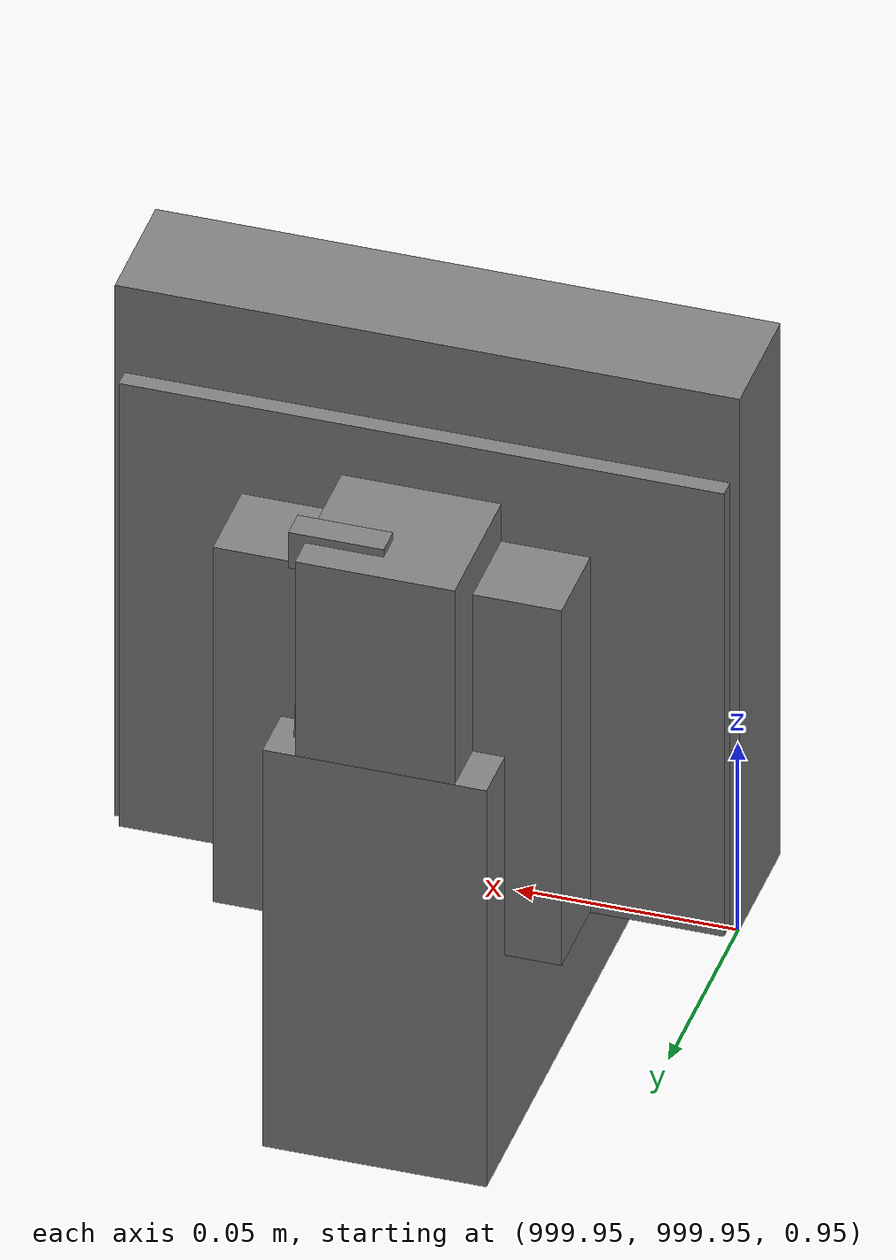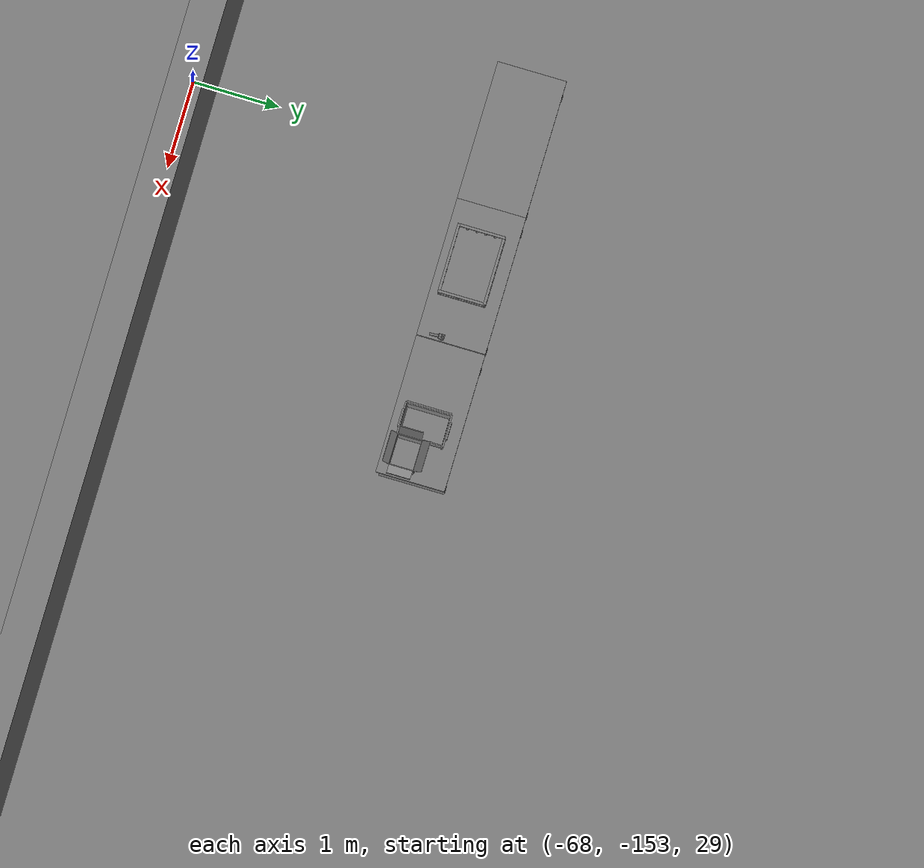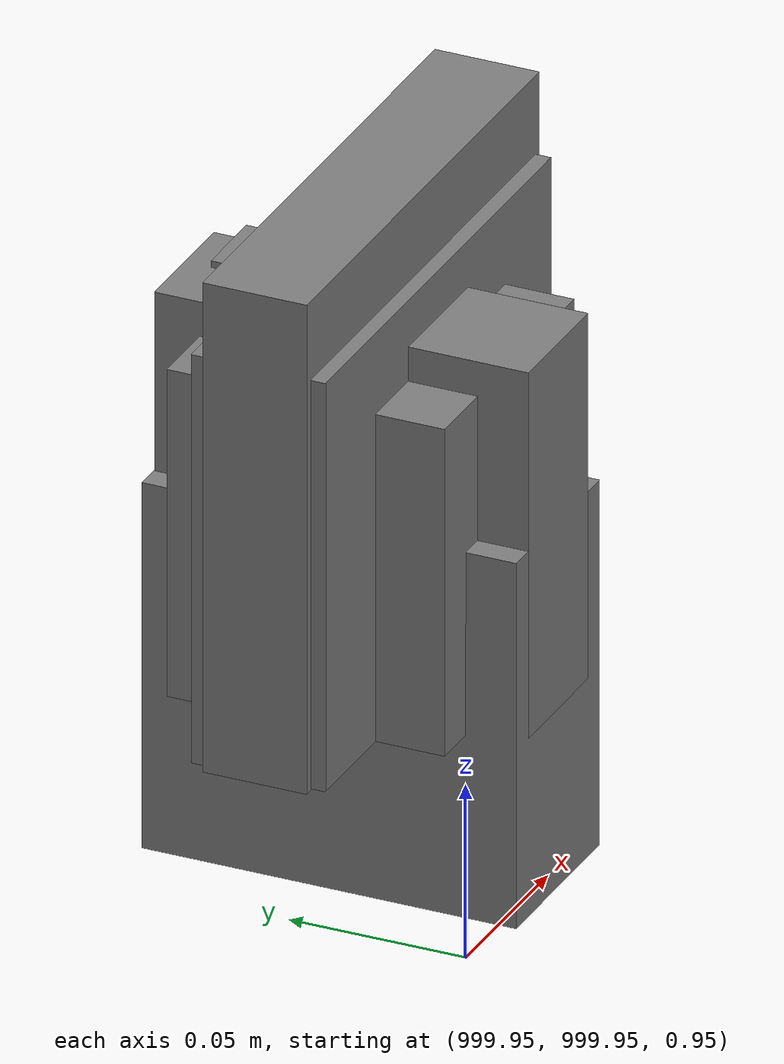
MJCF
<mujoco>
    <option gravity="0.000000000 0.000000000 -9.810000420" timestep="0.0049999999" integrator="implicitfast" density="1.225" viscosity="1.8000001e-05" noslip_iterations="10" iterations="100" sdf_iterations="50">
        <flag multiccd="disable"/>
    </option>
    <size memory="1000M"/>
    <compiler coordinate="local"/>
    <worldbody>
        <light cutoff="30" pos="0 1 1" dir="0 -1 -2"/>
        <light cutoff="30" pos="0 -1 1" dir="0 1 -2"/>
        <body pos="1000.000000000 1000.000000000 1.000000000" euler="0.000000000 0.000000000 180.000000000" name="openloong_gripper_2f85_fix_base_usda_cpu_fan">
            <geom contype="1" conaffinity="1" density="1000" type="box" material="" rgba="0.500000000 0.500000000 0.500000000 1.000000000" solimp="0.899999976 0.949999988 0.001000000" friction="1.000000000 0.005000000 0.000100000" solref="0.020000000 1.000000000" margin="0" condim="3" group="0" pos="0.000000000 0.000000000 0.070034981" quat="0.000000000 0.000000000 0.000000000 1.000000000" size="0.070700005 0.014699999 0.070700005" name="openloong_gripper_2f85_fix_base_usda_geom_835B11A0_2B7E_4DCF_9125_E2457E764355"/>
            <freejoint name="openloong_gripper_2f85_fix_base_usda_cpu_fan_joint"/>
            <site size="0.005000000 0.005000000 0.005000000" rgba="0.500000000 0.500000000 0.500000000 1.000000000" pos="0.000000000 0.000000000 0.000000000" quat="0.999961913 0.008726535 0.000000000 0.000000000" group="0" type="sphere" name="openloong_gripper_2f85_fix_base_usda_cpu_fancsite"/>
        </body>
        <body pos="1000.000000000 1000.000000000 1.000000000" euler="0.000000000 0.000000000 180.000000000" name="openloong_gripper_2f85_fix_base_usda_wifi_box">
            <geom contype="1" conaffinity="1" density="1000" type="box" material="" rgba="0.500000000 0.500000000 0.500000000 1.000000000" solimp="0.899999976 0.949999988 0.001000000" friction="1.000000000 0.005000000 0.000100000" solref="0.020000000 1.000000000" margin="0" condim="3" group="0" pos="0.000000000 0.000000000 0.058978677" quat="0.000000000 0.000000047 0.000000000 1.000000000" size="0.068499997 0.018999999 0.059000000" name="openloong_gripper_2f85_fix_base_usda_geom_1B3678BD_6A97_4328_BC7C_7E73525A8CA8"/>
            <freejoint name="openloong_gripper_2f85_fix_base_usda_wifi_box_joint"/>
            <site size="0.005000000 0.005000000 0.005000000" rgba="0.500000000 0.500000000 0.500000000 1.000000000" pos="0.000000000 0.000000000 0.000000000" quat="0.999961913 0.008726500 0.000000000 0.000000000" group="0" type="sphere" name="openloong_gripper_2f85_fix_base_usda_wifi_boxsite"/>
        </body>
        <body pos="-65.997825623 -148.919067383 31.164485931" euler="-22.229578018 -34.018642426 136.652893066" mocap="true" name="spotlight3_SpotLight"/>
        <body pos="1000.000000000 1000.000000000 1.000000000" euler="0.000000000 0.000000000 180.000000000" name="openloong_gripper_2f85_fix_base_usda_battery_01">
            <geom contype="1" conaffinity="1" density="1000" type="box" material="" rgba="0.500000000 0.500000000 0.500000000 1.000000000" solimp="0.899999976 0.949999988 0.001000000" friction="1.000000000 0.005000000 0.000100000" solref="0.020000000 1.000000000" margin="0" condim="3" group="0" pos="-0.011123657 -0.041940309 0.101691343" quat="1.000000000 0.000000000 0.000000000 0.000000000" size="0.010800000 0.003375000 0.004725000" name="openloong_gripper_2f85_fix_base_usda_geom_405297E3_31A0_4876_B42D_49F9D51F1439"/>
            <geom contype="1" conaffinity="1" density="1000" type="box" material="" rgba="0.500000000 0.500000000 0.500000000 1.000000000" solimp="0.899999976 0.949999988 0.001000000" friction="1.000000000 0.005000000 0.000100000" solref="0.020000000 1.000000000" margin="0" condim="3" group="0" pos="-0.010876465 -0.044247437 0.047066893" quat="0.998702705 -0.050920475 0.000000000 0.000000000" size="0.009450001 0.002700000 0.024975000" name="openloong_gripper_2f85_fix_base_usda_geom_3AC7FB42_6C48_4DE7_8258_653610DD404B"/>
            <geom contype="1" conaffinity="1" density="1000" type="box" material="" rgba="0.500000000 0.500000000 0.500000000 1.000000000" solimp="0.899999976 0.949999988 0.001000000" friction="1.000000000 0.005000000 0.000100000" solref="0.020000000 1.000000000" margin="0" condim="3" group="0" pos="-0.001235962 -0.000659180 0.047381196" quat="1.000000000 0.000000000 0.000000000 0.000000000" size="0.039420001 0.039150000 0.047250003" name="openloong_gripper_2f85_fix_base_usda_geom_A6197654_5455_4651_90D4_3B23C2CFD3E0"/>
            <geom contype="1" conaffinity="1" density="1000" type="box" material="" rgba="0.500000000 0.500000000 0.500000000 1.000000000" solimp="0.899999976 0.949999988 0.001000000" friction="1.000000000 0.005000000 0.000100000" solref="0.020000000 1.000000000" margin="0" condim="3" group="0" pos="-0.010876465 -0.039138794 0.009851727" quat="1.000000000 0.000000000 0.000000000 0.000000000" size="0.009450001 0.010800000 0.013500000" name="openloong_gripper_2f85_fix_base_usda_geom_C4DC5C0A_821E_49EF_BF79_0768D017C542"/>
            <geom contype="1" conaffinity="1" density="1000" type="box" material="" rgba="0.500000000 0.500000000 0.500000000 1.000000000" solimp="0.899999976 0.949999988 0.001000000" friction="1.000000000 0.005000000 0.000100000" solref="0.020000000 1.000000000" margin="0" condim="3" group="0" pos="-0.010876465 -0.041528322 0.071508206" quat="1.000000000 0.000000000 0.000000000 0.000000000" size="0.009450001 0.002700000 0.027000001" name="openloong_gripper_2f85_fix_base_usda_geom_18F08C87_FF09_42D8_88EF_9D5AA0FA85FA"/>
            <freejoint name="openloong_gripper_2f85_fix_base_usda_battery_01_joint"/>
            <site size="0.005000000 0.005000000 0.005000000" rgba="0.500000000 0.500000000 0.500000000 1.000000000" pos="0.000000000 0.000000000 0.000000000" quat="0.999961913 0.008726500 0.000000000 0.000000000" group="0" type="sphere" name="openloong_gripper_2f85_fix_base_usda_battery_01site"/>
        </body>
        <body pos="1000.000000000 1000.000000000 1.000000000" euler="0.000011953 0.000005123 -179.999984741" name="openloong_gripper_2f85_fix_base_usda_intel_box">
            <geom contype="1" conaffinity="1" density="1000" type="box" material="" rgba="0.500000000 0.500000000 0.500000000 1.000000000" solimp="0.899999976 0.949999988 0.001000000" friction="1.000000000 0.005000000 0.000100000" solref="0.020000000 1.000000000" margin="0" condim="3" group="0" pos="0.000000000 -0.000067139 0.000082284" quat="0.707106709 0.000000225 0.000000253 0.707106650" size="0.052800003 0.025300000 0.052800003" name="openloong_gripper_2f85_fix_base_usda_geom_6A7E6218_E931_444F_880D_A6CA91C327D1"/>
            <freejoint name="openloong_gripper_2f85_fix_base_usda_intel_box_joint"/>
            <site size="0.005000000 0.005000000 0.005000000" rgba="0.500000000 0.500000000 0.500000000 1.000000000" pos="0.000000000 0.000000000 0.000000000" quat="0.999961913 0.008726500 0.000000000 0.000000000" group="0" type="sphere" name="openloong_gripper_2f85_fix_base_usda_intel_boxsite"/>
        </body>
        <body pos="1000.000000000 999.999938965 1.000000000" euler="0.000000000 0.000000000 180.000000000" name="openloong_gripper_2f85_fix_base_usda_intelcore_i5">
            <geom contype="1" conaffinity="1" density="1000" type="box" material="" rgba="0.500000000 0.500000000 0.500000000 1.000000000" solimp="0.899999976 0.949999988 0.001000000" friction="1.000000000 0.005000000 0.000100000" solref="0.020000000 1.000000000" margin="0" condim="3" group="0" pos="0.000000000 0.000000000 0.051722717" quat="0.707106709 0.000000000 0.000000000 -0.707106769" size="0.052800000 0.018080002 0.052800000" name="openloong_gripper_2f85_fix_base_usda_geom_EF9C13D8_F513_47DF_B784_8A38890C2AF3"/>
            <freejoint name="openloong_gripper_2f85_fix_base_usda_intelcore_i5_joint"/>
            <site size="0.005000000 0.005000000 0.005000000" rgba="0.500000000 0.500000000 0.500000000 1.000000000" pos="0.000000000 0.000000000 0.000000000" quat="0.999961913 0.008726534 0.000000000 0.000000000" group="0" type="sphere" name="openloong_gripper_2f85_fix_base_usda_intelcore_i5site"/>
        </body>
        <body pos="-66.068580627 -149.687500000 31.166532516" euler="24.428812027 -84.881645203 167.797363281" mocap="true" name="spotlight2_SpotLight"/>
        <body pos="-66.220481873 -149.585937500 31.163665771" euler="13.485654831 -34.562191010 87.734710693" mocap="true" name="spotlight4_SpotLight"/>
        <body pos="-64.866622925 -149.383972168 30.183746338" euler="89.999984741 89.999946594 0.000000000" name="openloong_gripper_2f85_fix_base_usda_bluebox_01">
            <geom contype="1" conaffinity="1" density="1000" type="box" material="" rgba="0.500000000 0.500000000 0.500000000 1.000000000" solimp="0.899999976 0.949999988 0.001000000" friction="1.000000000 0.005000000 0.000100000" solref="0.020000000 1.000000000" margin="0" condim="3" group="0" pos="0.276580811 0.187225342 0.000068665" quat="0.707106948 0.000077471 0.707106352 0.000077486" size="0.100000001 0.057999998 0.010000000" name="openloong_gripper_2f85_fix_base_usda_geom_D9B46207_5B6A_41E4_A227_F1B525E21A35"/>
            <geom contype="1" conaffinity="1" density="1000" type="box" material="" rgba="0.500000000 0.500000000 0.500000000 1.000000000" solimp="0.899999976 0.949999988 0.001000000" friction="1.000000000 0.005000000 0.000100000" solref="0.020000000 1.000000000" margin="0" condim="3" group="0" pos="0.000000000 0.002883911 0.000000000" quat="0.999999881 0.000000000 0.000000000 0.000000000" size="0.254000008 0.003000000 0.172000006" name="openloong_gripper_2f85_fix_base_usda_geom_3423D80D_BF32_4C41_9137_4EC6C9B43133"/>
            <geom contype="1" conaffinity="1" density="1000" type="box" material="" rgba="0.500000000 0.500000000 0.500000000 1.000000000" solimp="0.899999976 0.949999988 0.001000000" friction="1.000000000 0.005000000 0.000100000" solref="0.020000000 1.000000000" margin="0" condim="3" group="0" pos="0.000000000 0.124874115 0.173484802" quat="0.999796331 0.020176515 -0.000000015 0.000000030" size="0.259999990 0.119999997 0.007000000" name="openloong_gripper_2f85_fix_base_usda_geom_BE648A11_F20B_4E3E_8B9E_0E880AE50CF2"/>
            <geom contype="1" conaffinity="1" density="1000" type="box" material="" rgba="0.500000000 0.500000000 0.500000000 1.000000000" solimp="0.899999976 0.949999988 0.001000000" friction="1.000000000 0.005000000 0.000100000" solref="0.020000000 1.000000000" margin="0" condim="3" group="0" pos="0.000000000 0.124874115 -0.173469543" quat="0.999796331 -0.020176545 -0.000000015 0.000000000" size="0.259999990 0.119999997 0.007000000" name="openloong_gripper_2f85_fix_base_usda_geom_E13E38E5_0B9B_487A_BF57_3B0630528A97"/>
            <geom contype="1" conaffinity="1" density="1000" type="box" material="" rgba="0.500000000 0.500000000 0.500000000 1.000000000" solimp="0.899999976 0.949999988 0.001000000" friction="1.000000000 0.005000000 0.000100000" solref="0.020000000 1.000000000" margin="0" condim="3" group="0" pos="0.000000000 0.214008331 0.188980103" quat="0.999912977 0.013176724 0.000000015 0.000000000" size="0.259999990 0.029999999 0.012500000" name="openloong_gripper_2f85_fix_base_usda_geom_7C75F9EF_DE0E_45A0_B9C6_2AF52CDD6FA6"/>
            <geom contype="1" conaffinity="1" density="1000" type="box" material="" rgba="0.500000000 0.500000000 0.500000000 1.000000000" solimp="0.899999976 0.949999988 0.001000000" friction="1.000000000 0.005000000 0.000100000" solref="0.020000000 1.000000000" margin="0" condim="3" group="0" pos="-0.258361816 0.125289917 0.001876831" quat="0.702796936 -0.020792112 0.710783124 0.020769298" size="0.189999998 0.119999997 0.009000000" name="openloong_gripper_2f85_fix_base_usda_geom_A350F207_4310_49AA_AB5C_EC37ED412E85"/>
            <geom contype="1" conaffinity="1" density="1000" type="box" material="" rgba="0.500000000 0.500000000 0.500000000 1.000000000" solimp="0.899999976 0.949999988 0.001000000" friction="1.000000000 0.005000000 0.000100000" solref="0.020000000 1.000000000" margin="0" condim="3" group="0" pos="0.000000000 0.214008331 -0.188980103" quat="0.999912977 -0.013176769 0.000000030 0.000000015" size="0.259999990 0.029999999 0.012500000" name="openloong_gripper_2f85_fix_base_usda_geom_44456A48_E8DD_4B4B_8BE2_C930E655ABD3"/>
            <geom contype="1" conaffinity="1" density="1000" type="box" material="" rgba="0.500000000 0.500000000 0.500000000 1.000000000" solimp="0.899999976 0.949999988 0.001000000" friction="1.000000000 0.005000000 0.000100000" solref="0.020000000 1.000000000" margin="0" condim="3" group="0" pos="-0.276611328 0.187225342 0.000068665" quat="0.707106650 0.000077441 0.707106709 0.000077456" size="0.100000001 0.057999998 0.010000000" name="openloong_gripper_2f85_fix_base_usda_geom_F5EEF3B9_42AB_4968_89CD_D2EC83DF399B"/>
            <geom contype="1" conaffinity="1" density="1000" type="box" material="" rgba="0.500000000 0.500000000 0.500000000 1.000000000" solimp="0.899999976 0.949999988 0.001000000" friction="1.000000000 0.005000000 0.000100000" solref="0.020000000 1.000000000" margin="0" condim="3" group="0" pos="0.258331299 0.125289917 0.001876831" quat="0.702851415 0.018856421 0.710823774 -0.019329369" size="0.189999998 0.119999997 0.009000000" name="openloong_gripper_2f85_fix_base_usda_geom_8B6769AE_8CFF_4909_8887_4973BDB6A06F"/>
            <freejoint name="openloong_gripper_2f85_fix_base_usda_bluebox_01_joint"/>
            <site size="0.005000000 0.005000000 0.005000000" rgba="0.500000000 0.500000000 0.500000000 1.000000000" pos="0.000000000 0.000000000 0.000000000" quat="0.999961913 0.008726534 0.000000000 0.000000000" group="0" type="sphere" name="openloong_gripper_2f85_fix_base_usda_bluebox_01site"/>
        </body>
        <body pos="-64.496299744 -149.491867065 30.235729218" euler="0.000000000 0.000000000 89.999946594" name="openloong_gripper_2f85_fix_base_usda_cardboardbox_01">
            <geom contype="1" conaffinity="1" density="1000" type="box" material="" rgba="0.500000000 0.500000000 0.500000000 1.000000000" solimp="0.899999976 0.949999988 0.001000000" friction="1.000000000 0.005000000 0.000100000" solref="0.020000000 1.000000000" margin="0" condim="3" group="0" pos="-0.003166199 -0.004086494 0.005052090" quat="1.000000000 0.000000000 0.000000000 0.000000000" size="0.142499998 0.177500010 0.005000000" name="openloong_gripper_2f85_fix_base_usda_geom_5278712C_21F7_4721_BA8C_CAE392EC5814"/>
            <geom contype="1" conaffinity="1" density="1000" type="box" material="" rgba="0.500000000 0.500000000 0.500000000 1.000000000" solimp="0.899999976 0.949999988 0.001000000" friction="1.000000000 0.005000000 0.000100000" solref="0.020000000 1.000000000" margin="0" condim="3" group="0" pos="-0.003166199 0.170316696 0.150570869" quat="1.000000000 0.000000000 0.000000000 0.000000000" size="0.142499998 0.005000000 0.149999991" name="openloong_gripper_2f85_fix_base_usda_geom_3F05BB7B_3019_4BF5_81C4_10A9BF7253E0"/>
            <geom contype="1" conaffinity="1" density="1000" type="box" material="" rgba="0.500000000 0.500000000 0.500000000 1.000000000" solimp="0.899999976 0.949999988 0.001000000" friction="1.000000000 0.005000000 0.000100000" solref="0.020000000 1.000000000" margin="0" condim="3" group="0" pos="-0.147399902 -0.005307198 0.150570869" quat="1.000000000 0.000000000 0.000000000 0.000000000" size="0.005000000 0.177500010 0.149999991" name="openloong_gripper_2f85_fix_base_usda_geom_999E8F7D_C1CE_4A90_8FC0_3B1C9BAE9872"/>
            <geom contype="1" conaffinity="1" density="1000" type="box" material="" rgba="0.500000000 0.500000000 0.500000000 1.000000000" solimp="0.899999976 0.949999988 0.001000000" friction="1.000000000 0.005000000 0.000100000" solref="0.020000000 1.000000000" margin="0" condim="3" group="0" pos="0.140275955 -0.005307198 0.150570869" quat="1.000000000 0.000000000 0.000000000 0.000000000" size="0.005000000 0.177500010 0.149999991" name="openloong_gripper_2f85_fix_base_usda_geom_DDCE774E_0518_4792_AAB5_7062906EE231"/>
            <geom contype="1" conaffinity="1" density="1000" type="box" material="" rgba="0.500000000 0.500000000 0.500000000 1.000000000" solimp="0.899999976 0.949999988 0.001000000" friction="1.000000000 0.005000000 0.000100000" solref="0.020000000 1.000000000" margin="0" condim="3" group="0" pos="-0.003166199 -0.181550980 0.150570869" quat="1.000000000 0.000000000 0.000000000 0.000000000" size="0.142499998 0.005000000 0.149999991" name="openloong_gripper_2f85_fix_base_usda_geom_BA145486_3E11_4545_A370_1C7E56F93942"/>
            <freejoint name="openloong_gripper_2f85_fix_base_usda_cardboardbox_01_joint"/>
            <site size="0.005000000 0.005000000 0.005000000" rgba="0.500000000 0.500000000 0.500000000 1.000000000" pos="0.000000000 0.000000000 0.000000000" quat="0.999961913 0.008726535 0.000000000 0.000000000" group="0" type="sphere" name="openloong_gripper_2f85_fix_base_usda_site_3F917789_72A6_495E_B351_476BDD4C92EF"/>
            <body pos="0.139160156 -0.004048347 0.301930904" euler="-179.999954224 49.383502960 179.999954224" name="openloong_gripper_2f85_fix_base_usda_A1_006">
                <geom contype="1" conaffinity="1" density="1000" type="box" material="" rgba="0.500000000 0.500000000 0.500000000 1.000000000" solimp="0.899999976 0.949999988 0.001000000" friction="1.000000000 0.005000000 0.000100000" solref="0.020000000 1.000000000" margin="0" condim="3" group="0" pos="-0.071587563 0.000009537 0.001745224" quat="0.999999881 0.000000000 0.000000000 0.000000000" size="0.071249999 0.179999992 0.002500000" name="openloong_gripper_2f85_fix_base_usda_geom_7A15A6D2_6655_4288_B091_434FFA566173"/>
                <joint armature="0" stiffness="0.07" damping="0.0099999998" axis="0.000000 1.000000 0.000000" type="hinge" name="openloong_gripper_2f85_fix_base_usda_A1_006"/>
            </body>
            <body pos="-0.145902634 -0.004086494 0.301938057" euler="-180.000000000 -60.000011444 -180.000000000" name="openloong_gripper_2f85_fix_base_usda_A2_006">
                <geom contype="1" conaffinity="1" density="1000" type="box" material="" rgba="0.500000000 0.500000000 0.500000000 1.000000000" solimp="0.899999976 0.949999988 0.001000000" friction="1.000000000 0.005000000 0.000100000" solref="0.020000000 1.000000000" margin="0" condim="3" group="0" pos="0.071268082 0.000009537 0.002717972" quat="0.000002921 0.000000000 -0.000000030 0.999999881" size="0.071249999 0.179999992 0.002500000" name="openloong_gripper_2f85_fix_base_usda_geom_782EF148_742C_4255_8AE6_545AE8634018"/>
                <joint armature="0" stiffness="0.07" damping="0.0099999998" axis="0.000000 1.000000 0.000000" type="hinge" name="openloong_gripper_2f85_fix_base_usda_A2_006"/>
            </body>
            <body pos="-0.003385544 0.175991058 0.301930904" euler="-125.858116150 -0.000004561 0.000002331" name="openloong_gripper_2f85_fix_base_usda_B2_006">
                <geom contype="1" conaffinity="1" density="1000" type="box" material="" rgba="0.500000000 0.500000000 0.500000000 1.000000000" solimp="0.899999976 0.949999988 0.001000000" friction="1.000000000 0.005000000 0.000100000" solref="0.020000000 1.000000000" margin="0" condim="3" group="0" pos="0.000009537 -0.070939064 -0.002470016" quat="0.999614120 0.027776197 -0.000000015 0.000000030" size="0.137500003 0.064999998 0.005000000" name="openloong_gripper_2f85_fix_base_usda_geom_03A51314_07B5_4FE1_AF87_1563973500A3"/>
                <joint armature="0" stiffness="0.07" damping="0.0099999998" axis="1.000000 0.000000 0.000000" type="hinge" name="openloong_gripper_2f85_fix_base_usda_B2_006"/>
            </body>
            <body pos="-0.003385544 -0.184140205 0.301938057" euler="147.805557251 0.000000000 0.000000000" name="openloong_gripper_2f85_fix_base_usda_B1_006">
                <geom contype="1" conaffinity="1" density="1000" type="box" material="" rgba="0.500000000 0.500000000 0.500000000 1.000000000" solimp="0.899999976 0.949999988 0.001000000" friction="1.000000000 0.005000000 0.000100000" solref="0.020000000 1.000000000" margin="0" condim="3" group="0" pos="-0.000028610 0.070202351 -0.002703667" quat="0.999614179 -0.027776167 0.000000000 0.000000000" size="0.137500003 0.064999998 0.005000000" name="openloong_gripper_2f85_fix_base_usda_geom_699BF679_3364_44F7_8900_4918F9D91EE1"/>
                <joint armature="0" stiffness="0.07" damping="0.0099999998" axis="1.000000 0.000000 0.000000" type="hinge" name="openloong_gripper_2f85_fix_base_usda_B1_006"/>
            </body>
        </body>
        <body pos="-65.882858276 -149.481979370 30.229999542" euler="-64.487716675 0.000000000 0.000000000" name="openloong_gripper_2f85_fix_base_usda_Barcode">
            <geom contype="1" conaffinity="1" density="1000" type="box" material="" rgba="0.500000000 0.500000000 0.500000000 1.000000000" solimp="0.899999976 0.949999988 0.001000000" friction="1.000000000 0.005000000 0.000100000" solref="0.020000000 1.000000000" margin="0" condim="3" group="0" pos="0.000000000 0.013038635 0.001419067" quat="0.000000000 0.000000000 0.000000000 1.000000119" size="0.034000002 0.010000000 0.017999999" name="openloong_gripper_2f85_fix_base_usda_geom_4B8638C3_2294_42EB_8FED_87DCC24146C2"/>
            <geom contype="1" conaffinity="1" density="1000" type="box" material="" rgba="0.500000000 0.500000000 0.500000000 1.000000000" solimp="0.899999976 0.949999988 0.001000000" friction="1.000000000 0.005000000 0.000100000" solref="0.020000000 1.000000000" margin="0" condim="3" group="0" pos="0.000000000 -0.035301208 -0.007095337" quat="0.000000000 0.000000000 -0.043619365 0.999048233" size="0.028999999 0.010000000 0.020000000" name="openloong_gripper_2f85_fix_base_usda_geom_1C593872_F6E9_457C_9D01_33740862741C"/>
            <geom contype="1" conaffinity="1" density="1000" type="box" material="" rgba="0.500000000 0.500000000 0.500000000 1.000000000" solimp="0.899999976 0.949999988 0.001000000" friction="1.000000000 0.005000000 0.000100000" solref="0.020000000 1.000000000" margin="0" condim="3" group="0" pos="0.000000000 -0.043411255 -0.011749268" quat="0.922262907 0.386563420 0.000000000 0.000000000" size="0.026000001 0.010000000 0.020000000" name="openloong_gripper_2f85_fix_base_usda_geom_94708917_EC77_499A_86C9_8CE9ED7DA297"/>
            <geom contype="1" conaffinity="1" density="1000" type="box" material="" rgba="0.500000000 0.500000000 0.500000000 1.000000000" solimp="0.899999976 0.949999988 0.001000000" friction="1.000000000 0.005000000 0.000100000" solref="0.020000000 1.000000000" margin="0" condim="3" group="0" pos="0.000000000 -0.016967773 -0.031860352" quat="0.000000000 0.000000000 0.000000000 1.000000119" size="0.008000000 0.010000000 0.013000000" name="openloong_gripper_2f85_fix_base_usda_geom_F8AEC3A7_BF78_484B_B4C7_09B174C604D2"/>
            <geom contype="1" conaffinity="1" density="1000" type="box" material="" rgba="0.500000000 0.500000000 0.500000000 1.000000000" solimp="0.899999976 0.949999988 0.001000000" friction="1.000000000 0.005000000 0.000100000" solref="0.020000000 1.000000000" margin="0" condim="3" group="0" pos="0.000000000 -0.001869202 0.000312805" quat="0.953716993 0.300705761 0.000000000 0.000000000" size="0.032000002 0.010000000 0.018999999" name="openloong_gripper_2f85_fix_base_usda_geom_2D13CA1F_27E2_4BC6_A353_64BBC3427E2E"/>
            <geom contype="1" conaffinity="1" density="1000" type="box" material="" rgba="0.500000000 0.500000000 0.500000000 1.000000000" solimp="0.899999976 0.949999988 0.001000000" friction="1.000000000 0.005000000 0.000100000" solref="0.020000000 1.000000000" margin="0" condim="3" group="0" pos="0.000000000 -0.019531250 -0.003173828" quat="0.953716993 0.300705761 0.000000000 0.000000000" size="0.030999999 0.010000000 0.020000000" name="openloong_gripper_2f85_fix_base_usda_geom_345D888B_FC48_4D25_AE4E_50DC881D5730"/>
            <geom contype="1" conaffinity="1" density="1000" type="box" material="" rgba="0.500000000 0.500000000 0.500000000 1.000000000" solimp="0.899999976 0.949999988 0.001000000" friction="1.000000000 0.005000000 0.000100000" solref="0.020000000 1.000000000" margin="0" condim="3" group="0" pos="0.000000000 -0.035301208 -0.007095337" quat="0.953716993 0.300705761 0.000000000 0.000000000" size="0.028999999 0.010000000 0.020000000" name="openloong_gripper_2f85_fix_base_usda_geom_05FB94FE_BC83_4733_8798_21FF2634B53D"/>
            <geom contype="1" conaffinity="1" density="1000" type="box" material="" rgba="0.500000000 0.500000000 0.500000000 1.000000000" solimp="0.899999976 0.949999988 0.001000000" friction="1.000000000 0.005000000 0.000100000" solref="0.020000000 1.000000000" margin="0" condim="3" group="0" pos="0.000000000 -0.042617798 -0.071121216" quat="0.000000000 0.000000000 0.000000000 1.000000119" size="0.013000000 0.021000000 0.059999999" name="openloong_gripper_2f85_fix_base_usda_geom_9D319A80_B45D_4239_AA1A_C32EA7935FEB"/>
            <freejoint name="openloong_gripper_2f85_fix_base_usda_Barcode_joint"/>
            <site size="0.005000000 0.005000000 0.005000000" rgba="0.500000000 0.500000000 0.500000000 1.000000000" pos="0.000000000 0.000000000 0.000000000" quat="1.000000000 0.000000000 0.000000000 0.000000000" group="0" type="sphere" name="openloong_gripper_2f85_fix_base_usda_Barcode_site"/>
        </body>
        <body pos="-66.745018005 -149.392349243 30.184000015" euler="0.000000000 0.000000000 89.999946594" name="[22329691069239]_Basket_01">
            <geom contype="1" conaffinity="1" density="1000" type="box" material="" rgba="0.500000000 0.500000000 0.500000000 1.000000000" solimp="0.899999976 0.949999988 0.001000000" friction="1.000000000 0.005000000 0.000100000" solref="0.020000000 1.000000000" margin="0" condim="3" group="0" pos="-0.052425385 0.389207840 0.089787483" quat="0.707107008 0.000000000 0.000000000 0.707106411" size="0.014249999 0.014249999 0.059999999" name="[22329691069239]_geom_067F151F_D8FF_4D46_96FB_74F571966DF0"/>
            <geom contype="1" conaffinity="1" density="1000" type="box" material="" rgba="0.500000000 0.500000000 0.500000000 1.000000000" solimp="0.899999976 0.949999988 0.001000000" friction="1.000000000 0.005000000 0.000100000" solref="0.020000000 1.000000000" margin="0" condim="3" group="0" pos="0.264015198 -0.133043289 0.089787483" quat="0.707107008 0.000000000 0.000000000 0.707106411" size="0.014249999 0.014249999 0.059999999" name="[22329691069239]_geom_4FF5FD5B_43CF_44D9_8AD7_9ABEB51E74A5"/>
            <geom contype="1" conaffinity="1" density="1000" type="box" material="" rgba="0.500000000 0.500000000 0.500000000 1.000000000" solimp="0.899999976 0.949999988 0.001000000" friction="1.000000000 0.005000000 0.000100000" solref="0.020000000 1.000000000" margin="0" condim="3" group="0" pos="-0.264015198 -0.265548706 0.089793205" quat="0.707107008 0.000000000 0.000000000 0.707106411" size="0.014249999 0.014249999 0.059999999" name="[22329691069239]_geom_3DF11AA0_C2B0_4B0E_AD91_32DEF6F9180B"/>
            <geom contype="1" conaffinity="1" density="1000" type="box" material="" rgba="0.500000000 0.500000000 0.500000000 1.000000000" solimp="0.899999976 0.949999988 0.001000000" friction="1.000000000 0.005000000 0.000100000" solref="0.020000000 1.000000000" margin="0" condim="3" group="0" pos="-0.160263062 -0.389322281 0.089793205" quat="0.707107008 0.000000000 0.000000000 0.707106411" size="0.014249999 0.014249999 0.059999999" name="[22329691069239]_geom_74B30729_E04B_4411_B459_27EFED51725D"/>
            <geom contype="1" conaffinity="1" density="1000" type="box" material="" rgba="0.500000000 0.500000000 0.500000000 1.000000000" solimp="0.899999976 0.949999988 0.001000000" friction="1.000000000 0.005000000 0.000100000" solref="0.020000000 1.000000000" margin="0" condim="3" group="0" pos="0.162265778 -0.389322281 0.089787483" quat="0.707107008 0.000000000 0.000000000 0.707106411" size="0.014249999 0.014249999 0.059999999" name="[22329691069239]_geom_ADAC8D1E_AD0D_425D_8023_269A897F6A09"/>
            <geom contype="1" conaffinity="1" density="1000" type="box" material="" rgba="0.500000000 0.500000000 0.500000000 1.000000000" solimp="0.899999976 0.949999988 0.001000000" friction="1.000000000 0.005000000 0.000100000" solref="0.020000000 1.000000000" margin="0" condim="3" group="0" pos="0.264015198 0.389207840 0.089787483" quat="0.707107008 0.000000000 0.000000000 0.707106411" size="0.014249999 0.014249999 0.059999999" name="[22329691069239]_geom_630C15D7_1E94_47DD_9D0C_4B65E2E8676A"/>
            <geom contype="1" conaffinity="1" density="1000" type="box" material="" rgba="0.500000000 0.500000000 0.500000000 1.000000000" solimp="0.899999976 0.949999988 0.001000000" friction="1.000000000 0.005000000 0.000100000" solref="0.020000000 1.000000000" margin="0" condim="3" group="0" pos="-0.264015198 -0.133043289 0.089793205" quat="0.707107008 0.000000000 0.000000000 0.707106411" size="0.014249999 0.014249999 0.059999999" name="[22329691069239]_geom_A114D24D_D6A9_4067_8923_43571B9D0937"/>
            <geom contype="1" conaffinity="1" density="1000" type="box" material="" rgba="0.500000000 0.500000000 0.500000000 1.000000000" solimp="0.899999976 0.949999988 0.001000000" friction="1.000000000 0.005000000 0.000100000" solref="0.020000000 1.000000000" margin="0" condim="3" group="0" pos="-0.264026642 0.269256592 0.089793205" quat="0.707107008 0.000000000 0.000000000 0.707106411" size="0.014249999 0.014249999 0.059999999" name="[22329691069239]_geom_27BA95D6_264E_457C_8B03_5CA9B8743E39"/>
            <geom contype="1" conaffinity="1" density="1000" type="box" material="" rgba="0.500000000 0.500000000 0.500000000 1.000000000" solimp="0.899999976 0.949999988 0.001000000" friction="1.000000000 0.005000000 0.000100000" solref="0.020000000 1.000000000" margin="0" condim="3" group="0" pos="0.054462433 0.389207840 0.089787483" quat="0.707107008 0.000000000 0.000000000 0.707106411" size="0.014249999 0.014249999 0.059999999" name="[22329691069239]_geom_B6AAAA3A_4418_4447_A01F_5DFC28BC256C"/>
            <geom contype="1" conaffinity="1" density="1000" type="box" material="" rgba="0.500000000 0.500000000 0.500000000 1.000000000" solimp="0.899999976 0.949999988 0.001000000" friction="1.000000000 0.005000000 0.000100000" solref="0.020000000 1.000000000" margin="0" condim="3" group="0" pos="0.054462433 -0.389322281 0.089787483" quat="0.707107008 0.000000000 0.000000000 0.707106411" size="0.014249999 0.014249999 0.059999999" name="[22329691069239]_geom_5B81E57D_A65A_42E7_B51E_5AFD4488D186"/>
            <geom contype="1" conaffinity="1" density="1000" type="box" material="" rgba="0.500000000 0.500000000 0.500000000 1.000000000" solimp="0.899999976 0.949999988 0.001000000" friction="1.000000000 0.005000000 0.000100000" solref="0.020000000 1.000000000" margin="0" condim="3" group="0" pos="0.264015198 0.269256592 0.089793205" quat="0.707107008 0.000000000 0.000000000 0.707106411" size="0.014249999 0.014249999 0.059999999" name="[22329691069239]_geom_772A600D_377D_42D0_B158_7068FAA24F2A"/>
            <geom contype="1" conaffinity="1" density="1000" type="box" material="" rgba="0.500000000 0.500000000 0.500000000 1.000000000" solimp="0.899999976 0.949999988 0.001000000" friction="1.000000000 0.005000000 0.000100000" solref="0.020000000 1.000000000" margin="0" condim="3" group="0" pos="0.264015198 -0.389322281 0.089787483" quat="0.707107008 0.000000000 0.000000000 0.707106411" size="0.014249999 0.014249999 0.059999999" name="[22329691069239]_geom_43F36C08_8B3E_49EA_B54D_4DD00CF86362"/>
            <geom contype="1" conaffinity="1" density="1000" type="box" material="" rgba="0.500000000 0.500000000 0.500000000 1.000000000" solimp="0.899999976 0.949999988 0.001000000" friction="1.000000000 0.005000000 0.000100000" solref="0.020000000 1.000000000" margin="0" condim="3" group="0" pos="0.000000000 0.000000000 0.015998840" quat="0.707107008 0.000000000 0.000000000 0.707106411" size="0.403499991 0.279000014 0.015750000" name="[22329691069239]_geom_212AED99_38B2_459E_AC0B_C8DD42F2ECCA"/>
            <geom contype="1" conaffinity="1" density="1000" type="box" material="" rgba="0.500000000 0.500000000 0.500000000 1.000000000" solimp="0.899999976 0.949999988 0.001000000" friction="1.000000000 0.005000000 0.000100000" solref="0.020000000 1.000000000" margin="0" condim="3" group="0" pos="0.000000000 -0.389476776 0.163619041" quat="0.707107008 0.000000000 0.000000000 0.707106411" size="0.015000000 0.277500004 0.015750000" name="[22329691069239]_geom_D5D5EE9B_560C_4B81_95F0_E07F530471B4"/>
            <geom contype="1" conaffinity="1" density="1000" type="box" material="" rgba="0.500000000 0.500000000 0.500000000 1.000000000" solimp="0.899999976 0.949999988 0.001000000" friction="1.000000000 0.005000000 0.000100000" solref="0.020000000 1.000000000" margin="0" condim="3" group="0" pos="0.162265778 0.389207840 0.089787483" quat="0.707107008 0.000000000 0.000000000 0.707106411" size="0.014249999 0.014249999 0.059999999" name="[22329691069239]_geom_799261D6_A909_4B6B_A988_99C6DB08FDA7"/>
            <geom contype="1" conaffinity="1" density="1000" type="box" material="" rgba="0.500000000 0.500000000 0.500000000 1.000000000" solimp="0.899999976 0.949999988 0.001000000" friction="1.000000000 0.005000000 0.000100000" solref="0.020000000 1.000000000" margin="0" condim="3" group="0" pos="0.000000000 0.389471054 0.163619041" quat="0.707107008 0.000000000 0.000000000 0.707106411" size="0.015000000 0.277500004 0.015750000" name="[22329691069239]_geom_017FC1A7_2F2C_4231_888D_0B38AD5FEBBC"/>
            <geom contype="1" conaffinity="1" density="1000" type="box" material="" rgba="0.500000000 0.500000000 0.500000000 1.000000000" solimp="0.899999976 0.949999988 0.001000000" friction="1.000000000 0.005000000 0.000100000" solref="0.020000000 1.000000000" margin="0" condim="3" group="0" pos="-0.263511658 0.000000000 0.163619041" quat="0.707107008 0.000000000 0.000000000 0.707106411" size="0.403499991 0.015000000 0.015750000" name="[22329691069239]_geom_287A2D39_375A_49C7_A350_612D75E897B2"/>
            <geom contype="1" conaffinity="1" density="1000" type="box" material="" rgba="0.500000000 0.500000000 0.500000000 1.000000000" solimp="0.899999976 0.949999988 0.001000000" friction="1.000000000 0.005000000 0.000100000" solref="0.020000000 1.000000000" margin="0" condim="3" group="0" pos="-0.264015198 0.141334534 0.089793205" quat="0.707107008 0.000000000 0.000000000 0.707106411" size="0.014249999 0.014249999 0.059999999" name="[22329691069239]_geom_BA4B1246_9A8E_4FC9_BF5E_CEBA33292F9A"/>
            <geom contype="1" conaffinity="1" density="1000" type="box" material="" rgba="0.500000000 0.500000000 0.500000000 1.000000000" solimp="0.899999976 0.949999988 0.001000000" friction="1.000000000 0.005000000 0.000100000" solref="0.020000000 1.000000000" margin="0" condim="3" group="0" pos="0.264015198 -0.265548706 0.089787483" quat="0.707107008 0.000000000 0.000000000 0.707106411" size="0.014249999 0.014249999 0.059999999" name="[22329691069239]_geom_C8365A7A_DC61_4BC3_BC5B_13F8191AF4B6"/>
            <geom contype="1" conaffinity="1" density="1000" type="box" material="" rgba="0.500000000 0.500000000 0.500000000 1.000000000" solimp="0.899999976 0.949999988 0.001000000" friction="1.000000000 0.005000000 0.000100000" solref="0.020000000 1.000000000" margin="0" condim="3" group="0" pos="-0.160263062 0.389207840 0.089787483" quat="0.707107008 0.000000000 0.000000000 0.707106411" size="0.014249999 0.014249999 0.059999999" name="[22329691069239]_geom_BA71C70A_413E_4433_9250_EFDF80CCC085"/>
            <geom contype="1" conaffinity="1" density="1000" type="box" material="" rgba="0.500000000 0.500000000 0.500000000 1.000000000" solimp="0.899999976 0.949999988 0.001000000" friction="1.000000000 0.005000000 0.000100000" solref="0.020000000 1.000000000" margin="0" condim="3" group="0" pos="-0.052425385 -0.389322281 0.089787483" quat="0.707107008 0.000000000 0.000000000 0.707106411" size="0.014249999 0.014249999 0.059999999" name="[22329691069239]_geom_83968E25_3BCD_4096_98B4_D0F3D014DF69"/>
            <geom contype="1" conaffinity="1" density="1000" type="box" material="" rgba="0.500000000 0.500000000 0.500000000 1.000000000" solimp="0.899999976 0.949999988 0.001000000" friction="1.000000000 0.005000000 0.000100000" solref="0.020000000 1.000000000" margin="0" condim="3" group="0" pos="-0.264026642 -0.389322281 0.089793205" quat="0.707107008 0.000000000 0.000000000 0.707106411" size="0.014249999 0.014249999 0.059999999" name="[22329691069239]_geom_35CBB7E4_5103_4A07_B1ED_C2121C8285FC"/>
            <geom contype="1" conaffinity="1" density="1000" type="box" material="" rgba="0.500000000 0.500000000 0.500000000 1.000000000" solimp="0.899999976 0.949999988 0.001000000" friction="1.000000000 0.005000000 0.000100000" solref="0.020000000 1.000000000" margin="0" condim="3" group="0" pos="0.264015198 0.141334534 0.089787483" quat="0.707107008 0.000000000 0.000000000 0.707106411" size="0.014249999 0.014249999 0.059999999" name="[22329691069239]_geom_83FDFEDF_3351_41A2_AE3F_8472ECA896B4"/>
            <geom contype="1" conaffinity="1" density="1000" type="box" material="" rgba="0.500000000 0.500000000 0.500000000 1.000000000" solimp="0.899999976 0.949999988 0.001000000" friction="1.000000000 0.005000000 0.000100000" solref="0.020000000 1.000000000" margin="0" condim="3" group="0" pos="-0.264015198 0.389207840 0.089793205" quat="0.707107008 0.000000000 0.000000000 0.707106411" size="0.014249999 0.014249999 0.059999999" name="[22329691069239]_geom_A3D82E68_029D_4663_AC59_B308EC05ABB4"/>
            <geom contype="1" conaffinity="1" density="1000" type="box" material="" rgba="0.500000000 0.500000000 0.500000000 1.000000000" solimp="0.899999976 0.949999988 0.001000000" friction="1.000000000 0.005000000 0.000100000" solref="0.020000000 1.000000000" margin="0" condim="3" group="0" pos="0.264015198 0.004480362 0.089787483" quat="0.707107008 0.000000000 0.000000000 0.707106411" size="0.014249999 0.014249999 0.059999999" name="[22329691069239]_geom_7CF21A7B_3348_4597_A008_4D6D67D7CE3C"/>
            <geom contype="1" conaffinity="1" density="1000" type="box" material="" rgba="0.500000000 0.500000000 0.500000000 1.000000000" solimp="0.899999976 0.949999988 0.001000000" friction="1.000000000 0.005000000 0.000100000" solref="0.020000000 1.000000000" margin="0" condim="3" group="0" pos="0.263694763 -0.000011444 0.163619041" quat="0.707107008 0.000000000 0.000000000 0.707106411" size="0.403499991 0.015000000 0.015750000" name="[22329691069239]_geom_8EA01396_BB6B_4C0D_A67B_1803027ED02D"/>
            <geom contype="1" conaffinity="1" density="1000" type="box" material="" rgba="0.500000000 0.500000000 0.500000000 1.000000000" solimp="0.899999976 0.949999988 0.001000000" friction="1.000000000 0.005000000 0.000100000" solref="0.020000000 1.000000000" margin="0" condim="3" group="0" pos="-0.264015198 0.004480362 0.089793205" quat="0.707107008 0.000000000 0.000000000 0.707106411" size="0.014249999 0.014249999 0.059999999" name="[22329691069239]_geom_5817E208_60FB_4E07_BC59_B292CABA8E92"/>
            <freejoint name="[22329691069239]_joint_F1467BD6_658C_41C0_A91B_E7514BACAB5F"/>
        </body>
        <body pos="0.000000000 0.000000000 0.000000000" euler="0.000000000 0.000000000 0.000000000" name="Static Objects_Static Objects">
            <geom contype="1" conaffinity="1" density="1000" type="box" material="" rgba="0.500000000 0.500000000 0.500000000 1.000000000" solimp="0.899999976 0.949999988 0.001000000" friction="1.000000000 0.005000000 0.000100000" solref="0.020000000 1.000000000" margin="0" condim="3" group="0" pos="-67.544113159 -149.365814209 29.727830887" quat="0.500000417 0.499999970 0.499999553 0.499999970" size="0.381000012 0.319999993 0.041000001" name="Static Objects_geom_B0CB2F98_9EEF_4222_A33B_8A3294391314"/>
            <geom contype="1" conaffinity="1" density="1000" type="box" material="" rgba="0.500000000 0.500000000 0.500000000 1.000000000" solimp="0.899999976 0.949999988 0.001000000" friction="1.000000000 0.005000000 0.000100000" solref="0.020000000 1.000000000" margin="0" condim="3" group="0" pos="-68.239501953 -149.365814209 30.086868286" quat="0.500000417 0.499999970 0.499999553 0.499999970" size="0.370999992 0.039500002 0.745000005" name="Static Objects_geom_C8518EB9_F42B_4496_8728_5973EDE756DA"/>
            <geom contype="1" conaffinity="1" density="1000" type="box" material="" rgba="0.500000000 0.500000000 0.500000000 1.000000000" solimp="0.899999976 0.949999988 0.001000000" friction="1.000000000 0.005000000 0.000100000" solref="0.020000000 1.000000000" margin="0" condim="3" group="0" pos="-68.239501953 -149.365814209 30.147235870" quat="0.500000417 0.499999970 0.499999553 0.499999970" size="0.400000006 0.022000000 0.800000012" name="Static Objects_geom_2E5D9EDC_73F4_408B_8B21_A149267D3D24"/>
            <geom contype="1" conaffinity="1" density="1000" type="box" material="" rgba="0.500000000 0.500000000 0.500000000 1.000000000" solimp="0.899999976 0.949999988 0.001000000" friction="1.000000000 0.005000000 0.000100000" solref="0.020000000 1.000000000" margin="0" condim="3" group="0" pos="-68.934890747 -149.365814209 29.727830887" quat="0.500000417 0.499999970 0.499999553 0.499999970" size="0.381000012 0.319999993 0.041000001" name="Static Objects_geom_692EDFE8_F42F_49DC_B28D_CBC7D21D4D6C"/>
            <geom contype="1" conaffinity="1" density="1000" type="box" material="" rgba="0.500000000 0.500000000 0.500000000 1.000000000" solimp="0.899999976 0.949999988 0.001000000" friction="1.000000000 0.005000000 0.000100000" solref="0.020000000 1.000000000" margin="0" condim="3" group="0" pos="-68.239501953 -149.365814209 29.561563492" quat="0.500000417 0.499999970 0.499999553 0.499999970" size="0.020000000 0.022000000 0.660000026" name="Static Objects_geom_0BE4E626_5129_488A_B560_004364E44B83"/>
            <geom contype="1" conaffinity="1" density="1000" type="box" material="" rgba="0.500000000 0.500000000 0.500000000 1.000000000" solimp="0.899999976 0.949999988 0.001000000" friction="1.000000000 0.005000000 0.000100000" solref="0.020000000 1.000000000" margin="0" condim="3" group="0" pos="-65.945671082 -149.365814209 29.727830887" quat="0.500000417 0.499999970 0.499999553 0.499999970" size="0.381000012 0.319999993 0.041000001" name="Static Objects_geom_43266309_2304_422E_B7A6_03DE0E067F1E"/>
            <geom contype="1" conaffinity="1" density="1000" type="box" material="" rgba="0.500000000 0.500000000 0.500000000 1.000000000" solimp="0.899999976 0.949999988 0.001000000" friction="1.000000000 0.005000000 0.000100000" solref="0.020000000 1.000000000" margin="0" condim="3" group="0" pos="-66.641059875 -149.365814209 30.086868286" quat="0.500000417 0.499999970 0.499999553 0.499999970" size="0.370999992 0.039500002 0.745000005" name="Static Objects_geom_042F27B7_6D19_4734_B248_94D2548D691C"/>
            <geom contype="1" conaffinity="1" density="1000" type="box" material="" rgba="0.500000000 0.500000000 0.500000000 1.000000000" solimp="0.899999976 0.949999988 0.001000000" friction="1.000000000 0.005000000 0.000100000" solref="0.020000000 1.000000000" margin="0" condim="3" group="0" pos="-66.641059875 -149.365814209 30.147235870" quat="0.500000417 0.499999970 0.499999553 0.499999970" size="0.400000006 0.022000000 0.800000012" name="Static Objects_geom_7B4C7C40_201E_429A_A05B_43BA61AA5DA7"/>
            <geom contype="1" conaffinity="1" density="1000" type="box" material="" rgba="0.500000000 0.500000000 0.500000000 1.000000000" solimp="0.899999976 0.949999988 0.001000000" friction="1.000000000 0.005000000 0.000100000" solref="0.020000000 1.000000000" margin="0" condim="3" group="0" pos="-67.336448669 -149.365814209 29.727830887" quat="0.500000417 0.499999970 0.499999553 0.499999970" size="0.381000012 0.319999993 0.041000001" name="Static Objects_geom_8F3E8066_BBD5_4879_8EC5_25AF42D5DC63"/>
            <geom contype="1" conaffinity="1" density="1000" type="box" material="" rgba="0.500000000 0.500000000 0.500000000 1.000000000" solimp="0.899999976 0.949999988 0.001000000" friction="1.000000000 0.005000000 0.000100000" solref="0.020000000 1.000000000" margin="0" condim="3" group="0" pos="-66.641059875 -149.365814209 29.561563492" quat="0.500000417 0.499999970 0.499999553 0.499999970" size="0.020000000 0.022000000 0.660000026" name="Static Objects_geom_03545DDE_FBBC_4823_918D_67F0A6976346"/>
            <geom contype="1" conaffinity="1" density="1000" type="box" material="" rgba="0.500000000 0.500000000 0.500000000 1.000000000" solimp="0.899999976 0.949999988 0.001000000" friction="1.000000000 0.005000000 0.000100000" solref="0.020000000 1.000000000" margin="0" condim="3" group="0" pos="-64.338577271 -149.365814209 29.727830887" quat="0.500000417 0.499999970 0.499999553 0.499999970" size="0.381000012 0.319999993 0.041000001" name="Static Objects_geom_F73613EB_ECAF_4CD8_AEC7_F66D61D3ADF1"/>
            <geom contype="1" conaffinity="1" density="1000" type="box" material="" rgba="0.500000000 0.500000000 0.500000000 1.000000000" solimp="0.899999976 0.949999988 0.001000000" friction="1.000000000 0.005000000 0.000100000" solref="0.020000000 1.000000000" margin="0" condim="3" group="0" pos="-65.033966064 -149.365814209 30.086868286" quat="0.500000417 0.499999970 0.499999553 0.499999970" size="0.370999992 0.039500002 0.745000005" name="Static Objects_geom_6F5BADB2_8F83_42F8_AFAF_38E0DD2A19C2"/>
            <geom contype="1" conaffinity="1" density="1000" type="box" material="" rgba="0.500000000 0.500000000 0.500000000 1.000000000" solimp="0.899999976 0.949999988 0.001000000" friction="1.000000000 0.005000000 0.000100000" solref="0.020000000 1.000000000" margin="0" condim="3" group="0" pos="-65.033966064 -149.365814209 30.147235870" quat="0.500000417 0.499999970 0.499999553 0.499999970" size="0.400000006 0.022000000 0.800000012" name="Static Objects_geom_50318F78_79D7_45C1_BB1C_E6BD9D8EA468"/>
            <geom contype="1" conaffinity="1" density="1000" type="box" material="" rgba="0.500000000 0.500000000 0.500000000 1.000000000" solimp="0.899999976 0.949999988 0.001000000" friction="1.000000000 0.005000000 0.000100000" solref="0.020000000 1.000000000" margin="0" condim="3" group="0" pos="-65.729354858 -149.365814209 29.727830887" quat="0.500000417 0.499999970 0.499999553 0.499999970" size="0.381000012 0.319999993 0.041000001" name="Static Objects_geom_CD331E82_01F8_4A8C_B08A_735F6AC5DB1B"/>
            <geom contype="1" conaffinity="1" density="1000" type="box" material="" rgba="0.500000000 0.500000000 0.500000000 1.000000000" solimp="0.899999976 0.949999988 0.001000000" friction="1.000000000 0.005000000 0.000100000" solref="0.020000000 1.000000000" margin="0" condim="3" group="0" pos="-65.033966064 -149.365814209 29.561563492" quat="0.500000417 0.499999970 0.499999553 0.499999970" size="0.020000000 0.022000000 0.660000026" name="Static Objects_geom_21F167CF_D804_42AA_AD75_867CCF2FC1A2"/>
            <geom contype="1" conaffinity="1" density="1000" type="box" material="" rgba="0.500000000 0.500000000 0.500000000 1.000000000" solimp="0.899999976 0.949999988 0.001000000" friction="1.000000000 0.005000000 0.000100000" solref="0.020000000 1.000000000" margin="0" condim="3" group="0" pos="-61.754566193 -137.853729248 33.906845093" quat="0.707107067 0.000000000 0.000000000 0.707106471" size="0.759999990 0.759999990 4.500000000" name="Static Objects_geom_CB7FBF02_5190_49A1_AB54_3F20ECC6C398"/>
            <geom contype="1" conaffinity="1" density="1000" type="box" material="" rgba="0.500000000 0.500000000 0.500000000 1.000000000" solimp="0.899999976 0.949999988 0.001000000" friction="1.000000000 0.005000000 0.000100000" solref="0.020000000 1.000000000" margin="0" condim="3" group="0" pos="-57.511135101 -144.927108765 31.707921982" quat="1.000000000 0.000000000 0.000000000 0.000000000" size="0.200000003 8.000000000 2.299999952" name="Static Objects_geom_7784B80A_E54F_48F4_BF0E_47CCA706CA42"/>
            <geom contype="1" conaffinity="1" density="1000" type="box" material="" rgba="0.500000000 0.500000000 0.500000000 1.000000000" solimp="0.899999976 0.949999988 0.001000000" friction="1.000000000 0.005000000 0.000100000" solref="0.020000000 1.000000000" margin="0" condim="3" group="0" pos="-80.517646790 -157.574050903 31.688196182" quat="0.707107067 0.000000000 0.000000000 0.707106471" size="0.600000024 0.600000024 2.299999952" name="Static Objects_geom_E348825A_E24B_41E3_A8A3_E8D5CD2A55A2"/>
            <geom contype="1" conaffinity="1" density="1000" type="box" material="" rgba="0.500000000 0.500000000 0.500000000 1.000000000" solimp="0.899999976 0.949999988 0.001000000" friction="1.000000000 0.005000000 0.000100000" solref="0.020000000 1.000000000" margin="0" condim="3" group="0" pos="-80.711044312 -147.414932251 31.666158676" quat="1.000000000 0.000000000 0.000000000 0.000000000" size="0.200000003 10.000000000 2.299999952" name="Static Objects_geom_67052D20_07F7_4833_B4D9_02B4579C3CC7"/>
            <geom contype="1" conaffinity="1" density="1000" type="box" material="" rgba="0.500000000 0.500000000 0.500000000 1.000000000" solimp="0.899999976 0.949999988 0.001000000" friction="1.000000000 0.005000000 0.000100000" solref="0.020000000 1.000000000" margin="0" condim="3" group="0" pos="-57.687217712 -137.434692383 31.688196182" quat="0.707107067 0.000000000 0.000000000 0.707106471" size="0.600000024 0.600000024 2.299999952" name="Static Objects_geom_68F2160A_B1D6_4651_8DC3_142F2C2B32C6"/>
            <geom contype="1" conaffinity="1" density="1000" type="box" material="" rgba="0.500000000 0.500000000 0.500000000 1.000000000" solimp="0.899999976 0.949999988 0.001000000" friction="1.000000000 0.005000000 0.000100000" solref="0.020000000 1.000000000" margin="0" condim="3" group="0" pos="-69.537033081 -140.263229370 31.714921951" quat="0.707107067 0.000000000 0.000000000 0.707106471" size="0.759999990 4.500000000 2.299999952" name="Static Objects_geom_74A9B51E_AEF8_48D0_A56C_56F69DECDFCF"/>
            <geom contype="1" conaffinity="1" density="1000" type="box" material="" rgba="0.500000000 0.500000000 0.500000000 1.000000000" solimp="0.899999976 0.949999988 0.001000000" friction="1.000000000 0.005000000 0.000100000" solref="0.020000000 1.000000000" margin="0" condim="3" group="0" pos="-80.073638916 -137.853713989 33.906845093" quat="0.707107067 0.000000000 0.000000000 0.707106471" size="0.759999990 0.759999990 4.500000000" name="Static Objects_geom_CF9D767F_2010_47D9_859F_1958F6A0B487"/>
            <geom contype="1" conaffinity="1" density="1000" type="box" material="" rgba="0.500000000 0.500000000 0.500000000 1.000000000" solimp="0.899999976 0.949999988 0.001000000" friction="1.000000000 0.005000000 0.000100000" solref="0.020000000 1.000000000" margin="0" condim="3" group="0" pos="-73.406707764 -155.734664917 31.707921982" quat="1.000000000 0.000000000 0.000000000 0.000000000" size="0.200000003 3.000000000 2.299999952" name="Static Objects_geom_B78A4EBE_83DB_482F_9EB0_BA2AEA9CF303"/>
            <geom contype="1" conaffinity="1" density="1000" type="box" material="" rgba="0.500000000 0.500000000 0.500000000 1.000000000" solimp="0.899999976 0.949999988 0.001000000" friction="1.000000000 0.005000000 0.000100000" solref="0.020000000 1.000000000" margin="0" condim="3" group="0" pos="-68.497543335 -137.448257446 31.707921982" quat="0.707107067 0.000000000 0.000000000 0.707106471" size="0.200000003 14.000000000 2.299999952" name="Static Objects_geom_A31CD62C_2936_4EDA_AC11_437295949650"/>
            <geom contype="1" conaffinity="1" density="1000" type="cylinder" material="" rgba="0.500000000 0.500000000 0.500000000 1.000000000" solimp="0.899999976 0.949999988 0.001000000" friction="1.000000000 0.005000000 0.000100000" solref="0.020000000 1.000000000" margin="0" condim="3" group="0" pos="-68.868522644 -142.134506226 31.711090088" quat="0.707107067 0.000000000 0.000000000 0.707106471" size="0.509999990 2.299999952 1.000000000" name="Static Objects_geom_61175523_E6A0_4A52_BDC2_609355064A59"/>
            <geom contype="1" conaffinity="1" density="1000" type="plane" material="" rgba="0.500000000 0.500000000 0.500000000 1.000000000" solimp="0.899999976 0.949999988 0.001000000" friction="1.000000000 0.005000000 0.000100000" solref="0.020000000 1.000000000" margin="0" condim="3" group="0" pos="-72.873703003 -147.131927490 29.409669876" quat="1.000000000 0.000000000 0.000000000 0.000000000" size="18.000000000 14.000000000 1.000000000" name="Static Objects_geom_127217FF_D795_46D6_8555_809C785194F0"/>
            <geom contype="1" conaffinity="1" density="1000" type="box" material="" rgba="0.500000000 0.500000000 0.500000000 1.000000000" solimp="0.899999976 0.949999988 0.001000000" friction="1.000000000 0.005000000 0.000100000" solref="0.020000000 1.000000000" margin="0" condim="3" group="0" pos="-79.943580627 -157.782272339 31.707921982" quat="0.707107067 0.000000000 0.000000000 0.707106471" size="0.200000003 7.000000000 2.299999952" name="Static Objects_geom_595E251D_7052_48E7_A54E_4341429C490C"/>
            <geom contype="1" conaffinity="1" density="1000" type="box" material="" rgba="0.500000000 0.500000000 0.500000000 1.000000000" solimp="0.899999976 0.949999988 0.001000000" friction="1.000000000 0.005000000 0.000100000" solref="0.020000000 1.000000000" margin="0" condim="3" group="0" pos="-65.421028137 -152.903442383 31.707921982" quat="0.707107067 0.000000000 0.000000000 0.707106471" size="0.200000003 7.800000191 2.299999952" name="Static Objects_geom_DC64EECE_44FD_4B0F_88E0_F63DE80C07A5"/>
            <geom contype="1" conaffinity="1" density="1000" type="box" material="" rgba="0.500000000 0.500000000 0.500000000 1.000000000" solimp="0.899999976 0.949999988 0.001000000" friction="1.000000000 0.005000000 0.000100000" solref="0.020000000 1.000000000" margin="0" condim="3" group="0" pos="-74.776908875 -149.964416504 31.688196182" quat="1.000000000 0.000000000 0.000000000 0.000000000" size="0.600000024 0.409999996 2.299999952" name="Static Objects_geom_6D84F870_01F6_49B5_BCE2_D4BDCF0C3786"/>
            <geom contype="1" conaffinity="1" density="1000" type="cylinder" material="" rgba="0.500000000 0.500000000 0.500000000 1.000000000" solimp="0.899999976 0.949999988 0.001000000" friction="1.000000000 0.005000000 0.000100000" solref="0.020000000 1.000000000" margin="0" condim="3" group="0" pos="-60.161884308 -142.134506226 31.711090088" quat="0.707107067 0.000000000 0.000000000 0.707106471" size="0.509999990 2.299999952 1.000000000" name="Static Objects_geom_954B8F84_B6F4_45F9_B638_A29856BA2C9F"/>
            <geom contype="1" conaffinity="1" density="1000" type="cylinder" material="" rgba="0.500000000 0.500000000 0.500000000 1.000000000" solimp="0.899999976 0.949999988 0.001000000" friction="1.000000000 0.005000000 0.000100000" solref="0.020000000 1.000000000" margin="0" condim="3" group="0" pos="-75.382453918 -149.963455200 31.711090088" quat="0.707107067 0.000000000 0.000000000 0.707106471" size="0.409999996 2.299999952 1.000000000" name="Static Objects_geom_54F73B7B_D8CE_45F2_93DE_F845ABDDD7EF"/>
            <geom contype="1" conaffinity="1" density="1000" type="cylinder" material="" rgba="0.500000000 0.500000000 0.500000000 1.000000000" solimp="0.899999976 0.949999988 0.001000000" friction="1.000000000 0.005000000 0.000100000" solref="0.020000000 1.000000000" margin="0" condim="3" group="0" pos="-74.154960632 -149.963455200 31.711090088" quat="0.707107067 0.000000000 0.000000000 0.707106471" size="0.409999996 2.299999952 1.000000000" name="Static Objects_geom_56F5D6CC_EF40_4CC5_B6D8_292B3E01667B"/>
            <geom contype="1" conaffinity="1" density="1000" type="cylinder" material="" rgba="0.500000000 0.500000000 0.500000000 1.000000000" solimp="0.899999976 0.949999988 0.001000000" friction="1.000000000 0.005000000 0.000100000" solref="0.020000000 1.000000000" margin="0" condim="3" group="0" pos="-77.566612244 -142.134506226 31.711090088" quat="0.707107067 0.000000000 0.000000000 0.707106471" size="0.509999990 2.299999952 1.000000000" name="Static Objects_geom_0C31B8A0_C353_42A2_94C4_22EF22ACCBD0"/>
        </body>
        <body pos="-66.291030884 -149.869689941 29.018842697" euler="0.000000000 0.000000000 89.999946594" mocap="true" name="openloong_gripper_2f85_fix_base_usda_leftHandMocap"/>
        <body pos="-66.291030884 -149.869689941 29.018842697" euler="0.000000000 0.000000000 89.999946594" mocap="true" name="openloong_gripper_2f85_fix_base_usda_rightHandMocap"/>
        <body pos="-66.291030884 -149.869689941 30.218843460" euler="0.000000000 0.000000000 89.999946594" name="openloong_gripper_2f85_fix_base_usda_base_link">
            <geom contype="1" conaffinity="1" density="1000" type="mesh" material="" rgba="0.783999979 0.783999979 0.783999979 1.000000000" solimp="0.899999976 0.949999988 0.001000000" friction="1.000000000 0.005000000 0.000100000" solref="0.020000000 1.000000000" margin="0" condim="3" group="3" mesh="base_link" pos="0.000000000 0.000000000 0.000000000" quat="1.000000000 0.000000000 0.000000000 0.000000000" size="1.000000000 1.000000000 1.000000000" name="openloong_gripper_2f85_fix_base_usda__geom_7_65C65CD3_F3E3_4140_AECF_0FC802371845"/>
            <site size="0.005000000 0.005000000 0.005000000" rgba="0.500000000 0.500000000 0.500000000 1.000000000" pos="0.000000000 0.000000000 0.000000000" quat="1.000000000 0.000000000 0.000000000 0.000000000" group="0" type="sphere" name="openloong_gripper_2f85_fix_base_usda_imu"/>
            <inertial mass="22.447001" pos="-0.005664100 -0.001336700 0.238289997" diaginertia="0.374352545 0.277180195 0.220617250" quat="0.999247074 0.035235517 -0.015086859 0.006023135"/>
            <body pos="0.000000000 0.000000000 0.299997330" euler="0.000000000 0.000000000 0.000000000" name="openloong_gripper_2f85_fix_base_usda_dummy_body">
                <geom contype="1" conaffinity="1" density="1000" type="sphere" material="" rgba="0.783999979 0.783999979 0.783999979 1.000000000" solimp="0.899999976 0.949999988 0.001000000" friction="1.000000000 0.005000000 0.000100000" solref="0.020000000 1.000000000" margin="0" condim="3" group="3" pos="0.000000000 0.000000000 0.000000000" quat="1.000000000 0.000000000 0.000000000 0.000000000" size="0.010000000 0.000000000 0.000000000" name="openloong_gripper_2f85_fix_base_usda__geom_8_A516BE55_8248_41A9_A17E_EBF62EA22905"/>
                <joint armature="0.0099999998" stiffness="0" damping="0.1" axis="0.000000 0.000000 1.000000" type="hinge" name="openloong_gripper_2f85_fix_base_usda_dummy_joint"/>
                <site size="0.010000000 0.005000000 0.005000000" rgba="0.500000000 0.500000000 0.500000000 1.000000000" pos="0.000000000 0.000000000 0.000000000" quat="1.000000000 0.000000000 0.000000000 0.000000000" group="3" type="sphere" name="openloong_gripper_2f85_fix_base_usda_dummy_site"/>
            </body>
            <body pos="0.009002686 0.000000000 0.406400681" euler="0.000000000 0.000000000 0.000000000" name="openloong_gripper_2f85_fix_base_usda_Link_head_yaw">
                <geom contype="1" conaffinity="1" density="1000" type="mesh" material="" rgba="0.783999979 0.783999979 0.783999979 1.000000000" solimp="0.899999976 0.949999988 0.001000000" friction="1.000000000 0.005000000 0.000100000" solref="0.020000000 1.000000000" margin="0" condim="3" group="3" mesh="Link_head_yaw" pos="0.000000000 0.000000000 0.000000000" quat="1.000000000 0.000000000 0.000000000 0.000000000" size="1.000000000 1.000000000 1.000000000" name="openloong_gripper_2f85_fix_base_usda__geom_10_E8C865FE_6F38_4A08_AC02_199F17FA2E1D"/>
                <inertial mass="0.84249002" pos="0.000000000 -0.002081400 0.044801001" diaginertia="0.000700588 0.000629000 0.000553812" quat="0.706933022 -0.015675601 0.015677100 0.706933022"/>
                <body pos="0.000000000 -0.034599304 0.048500061" euler="0.000000000 0.000000000 0.000000000" name="openloong_gripper_2f85_fix_base_usda_Link_head_pitch">
                    <geom contype="1" conaffinity="1" density="1000" type="mesh" material="" rgba="0.783999979 0.783999979 0.783999979 1.000000000" solimp="0.899999976 0.949999988 0.001000000" friction="1.000000000 0.005000000 0.000100000" solref="0.020000000 1.000000000" margin="0" condim="3" group="3" mesh="Link_head_pitch" pos="0.000000000 0.000000000 0.000000000" quat="1.000000000 0.000000000 0.000000000 0.000000000" size="1.000000000 1.000000000 1.000000000" name="openloong_gripper_2f85_fix_base_usda__geom_12_F30FE6C9_241B_464E_BF12_70511C7D79CE"/>
                    <inertial mass="1.3943" pos="0.020569000 0.033004001 0.125000000" diaginertia="0.006381400 0.006289940 0.004481460" quat="0.973390222 0.008406822 0.228157058 0.019624906"/>
                    <body pos="0.000000000 0.029998779 0.000000000" euler="0.000000000 0.000000000 0.000000000" name="openloong_gripper_2f85_fix_base_usda_neck_center_body">
                        <site size="0.010000000 0.005000000 0.005000000" rgba="0.500000000 0.500000000 0.500000000 1.000000000" pos="0.000000000 0.000000000 0.000000000" quat="1.000000000 0.000000000 0.000000000 0.000000000" group="3" type="sphere" name="openloong_gripper_2f85_fix_base_usda_neck_center_site"/>
                        <body pos="0.020004272 0.000000000 0.149999619" euler="-0.000002229 39.998176575 -90.000205994" name="openloong_gripper_2f85_fix_base_usda_camera_head">
                            <site size="0.010000000 0.005000000 0.005000000" rgba="0.500000000 0.500000000 0.500000000 1.000000000" pos="0.000000000 0.000000000 0.000000000" quat="1.000000000 0.000000000 0.000000000 0.000000000" group="3" type="sphere" name="openloong_gripper_2f85_fix_base_usda_camera_head_site"/>
                        </body>
                    </body>
                </body>
            </body>
            <body pos="0.003997803 -0.161598206 0.392200470" euler="0.000000000 0.000000000 0.000000000" name="openloong_gripper_2f85_fix_base_usda_Link_arm_r_01">
                <geom contype="1" conaffinity="1" density="1000" type="mesh" material="" rgba="0.783999979 0.783999979 0.783999979 1.000000000" solimp="0.899999976 0.949999988 0.001000000" friction="1.000000000 0.005000000 0.000100000" solref="0.020000000 1.000000000" margin="0" condim="3" group="3" mesh="Link_arm_r_01" pos="0.000000000 0.000000000 0.000000000" quat="1.000000000 0.000000000 0.000000000 0.000000000" size="1.000000000 1.000000000 1.000000000" name="openloong_gripper_2f85_fix_base_usda__geom_14_90A89FE7_A6A4_441E_92FB_EB90D03A547C"/>
                <joint armature="0.0099999998" stiffness="0" damping="1" axis="0.000000 -1.000000 0.000000" limited="true" range="-170.000015259 170.000015259" type="hinge" name="openloong_gripper_2f85_fix_base_usda_J_arm_r_01"/>
                <inertial mass="0.75641" pos="0.004494600 -0.038293999 -0.000001874" diaginertia="0.000842990 0.000803050 0.000587120" quat="-0.000163502 0.707098067 0.000812463 0.707115054"/>
                <body pos="-0.041992188 -0.041000366 0.000000000" euler="0.000000000 0.000000000 0.000000000" name="openloong_gripper_2f85_fix_base_usda_Link_arm_r_02">
                    <geom contype="1" conaffinity="1" density="1000" type="mesh" material="" rgba="0.783999979 0.783999979 0.783999979 1.000000000" solimp="0.899999976 0.949999988 0.001000000" friction="1.000000000 0.005000000 0.000100000" solref="0.020000000 1.000000000" margin="0" condim="3" group="3" mesh="Link_arm_r_02" pos="0.000000000 0.000000000 0.000000000" quat="1.000000000 0.000000000 0.000000000 0.000000000" size="1.000000000 1.000000000 1.000000000" name="openloong_gripper_2f85_fix_base_usda__geom_16_5321F702_1516_4507_ABF5_2EB5C041B194"/>
                    <joint armature="0.0099999998" stiffness="0" damping="1" axis="-1.000000 0.000000 0.000000" limited="true" range="-105.000244141 105.000244141" type="hinge" name="openloong_gripper_2f85_fix_base_usda_J_arm_r_02"/>
                    <inertial mass="0.98500001" pos="0.041999999 -0.067430697 0.000000000" diaginertia="0.002262690 0.001730990 0.001154020" quat="0.500000000 0.500000000 -0.500000000 0.500000000"/>
                    <body pos="0.041992188 -0.122596741 0.000000000" euler="0.000000000 0.000000000 0.000000000" name="openloong_gripper_2f85_fix_base_usda_Link_arm_r_03">
                        <geom contype="1" conaffinity="1" density="1000" type="mesh" material="" rgba="0.783999979 0.783999979 0.783999979 1.000000000" solimp="0.899999976 0.949999988 0.001000000" friction="1.000000000 0.005000000 0.000100000" solref="0.020000000 1.000000000" margin="0" condim="3" group="3" mesh="Link_arm_r_03" pos="0.000000000 0.000000000 0.000000000" quat="1.000000000 0.000000000 0.000000000 0.000000000" size="1.000000000 1.000000000 1.000000000" name="openloong_gripper_2f85_fix_base_usda__geom_18_E19C86F3_3A1D_4A85_AD6F_FEE8ED7F80D1"/>
                        <joint armature="0.0099999998" stiffness="0" damping="1" axis="0.000000 -1.000000 0.000000" limited="true" range="-170.000015259 170.000015259" type="hinge" name="openloong_gripper_2f85_fix_base_usda_J_arm_r_03"/>
                        <inertial mass="0.95899999" pos="-0.001413580 -0.164663002 0.020757901" diaginertia="0.002101340 0.002064590 0.000754802" quat="0.560480952 0.454391927 -0.443732947 0.531497955"/>
                        <body pos="0.035293579 -0.177406311 0.023998260" euler="0.000000000 0.000000000 0.000000000" name="openloong_gripper_2f85_fix_base_usda_Link_arm_r_04">
                            <geom contype="1" conaffinity="1" density="1000" type="mesh" material="" rgba="0.783999979 0.783999979 0.783999979 1.000000000" solimp="0.899999976 0.949999988 0.001000000" friction="1.000000000 0.005000000 0.000100000" solref="0.020000000 1.000000000" margin="0" condim="3" group="3" mesh="Link_arm_r_04" pos="0.000000000 0.000000000 0.000000000" quat="1.000000000 0.000000000 0.000000000 0.000000000" size="1.000000000 1.000000000 1.000000000" name="openloong_gripper_2f85_fix_base_usda__geom_20_132B1C94_6C10_4EBB_B20D_1A7FF4991887"/>
                            <joint armature="0.0099999998" stiffness="0" damping="1" axis="-1.000000 0.000000 0.000000" limited="true" range="0.000000000 170.000015259" type="hinge" name="openloong_gripper_2f85_fix_base_usda_J_arm_r_04"/>
                            <inertial mass="0.60000002" pos="-0.038727000 -0.060766999 -0.021003000" diaginertia="0.001092610 0.000712422 0.000645102" quat="0.327701002 0.632602990 -0.467366993 0.523443997"/>
                            <body pos="-0.035293579 -0.103492737 -0.023998260" euler="0.000000000 0.000000000 0.000000000" name="openloong_gripper_2f85_fix_base_usda_Link_arm_r_05">
                                <geom contype="1" conaffinity="1" density="1000" type="mesh" material="" rgba="0.783999979 0.783999979 0.783999979 1.000000000" solimp="0.899999976 0.949999988 0.001000000" friction="1.000000000 0.005000000 0.000100000" solref="0.020000000 1.000000000" margin="0" condim="3" group="3" mesh="Link_arm_r_05" pos="0.000000000 0.000000000 0.000000000" quat="1.000000000 0.000000000 0.000000000 0.000000000" size="1.000000000 1.000000000 1.000000000" name="openloong_gripper_2f85_fix_base_usda__geom_22_145E6E05_14FA_49C7_A729_45F03FDD15CB"/>
                                <joint armature="0.0099999998" stiffness="0" damping="1" axis="0.000000 -1.000000 0.000000" limited="true" range="-170.000015259 170.000015259" type="hinge" name="openloong_gripper_2f85_fix_base_usda_J_arm_r_05"/>
                                <inertial mass="0.68976003" pos="0.000032712 -0.068658002 -0.000111780" diaginertia="0.002522510 0.002411100 0.000448695" quat="0.707660973 0.706543028 -0.002603360 0.002470550"/>
                                <body pos="-0.026489258 -0.196502686 0.000000000" euler="0.000000000 0.000000000 0.000000000" name="openloong_gripper_2f85_fix_base_usda_Link_arm_r_06">
                                    <geom contype="1" conaffinity="1" density="1000" type="mesh" material="" rgba="0.783999979 0.783999979 0.783999979 1.000000000" solimp="0.899999976 0.949999988 0.001000000" friction="1.000000000 0.005000000 0.000100000" solref="0.020000000 1.000000000" margin="0" condim="3" group="3" mesh="Link_arm_r_06" pos="0.000000000 0.000000000 0.000000000" quat="1.000000000 0.000000000 0.000000000 0.000000000" size="1.000000000 1.000000000 1.000000000" name="openloong_gripper_2f85_fix_base_usda__geom_24_1528B1E8_4154_42D4_AD4A_65DA482FCA6E"/>
                                    <joint armature="0.0099999998" stiffness="0" damping="1" axis="1.000000 0.000000 0.000000" limited="true" range="-105.000244141 105.000244141" type="hinge" name="openloong_gripper_2f85_fix_base_usda_J_arm_r_06"/>
                                    <inertial mass="0.28" pos="0.026078001 -0.000000896 0.001663700" diaginertia="0.000156930 0.000145601 0.000104979" quat="0.707080841 0.001851080 0.001883810 0.707127810"/>
                                    <body pos="0.026489258 0.000000000 0.031799316" euler="0.000000000 0.000000000 0.000000000" name="openloong_gripper_2f85_fix_base_usda_Link_arm_r_07">
                                        <geom contype="1" conaffinity="1" density="1000" type="mesh" material="" rgba="0.783999979 0.783999979 0.783999979 1.000000000" solimp="0.899999976 0.949999988 0.001000000" friction="1.000000000 0.005000000 0.000100000" solref="0.020000000 1.000000000" margin="0" condim="3" group="3" mesh="Link_arm_r_07" pos="0.000000000 0.000000000 0.000000000" quat="1.000000000 0.000000000 0.000000000 0.000000000" size="1.000000000 1.000000000 1.000000000" name="openloong_gripper_2f85_fix_base_usda__geom_26_B821F28E_DA9B_4A41_BBFD_CAEAA983767E"/>
                                        <joint armature="0.0099999998" stiffness="0" damping="1" axis="0.000000 0.000000 1.000000" limited="true" range="-60.000133514 60.000133514" type="hinge" name="openloong_gripper_2f85_fix_base_usda_J_arm_r_07"/>
                                        <inertial mass="0.61353999" pos="-0.007859000 -0.158170000 -0.027736001" diaginertia="0.003037610 0.002570910 0.000729379" quat="0.427542925 0.443532884 -0.553093910 0.560867906"/>
                                        <body pos="0.000000000 0.286994934 -0.270000458" euler="150.000350952 -0.000001649 -0.000000442" name="openloong_gripper_2f85_fix_base_usda_camera_wrist_r">
                                            <site size="0.010000000 0.005000000 0.005000000" rgba="0.500000000 0.500000000 0.500000000 1.000000000" pos="0.000000000 0.000000000 0.000000000" quat="1.000000000 0.000000000 0.000000000 0.000000000" group="3" type="sphere" name="openloong_gripper_2f85_fix_base_usda_camera_wrist_r_site"/>
                                        </body>
                                        <body pos="0.000000000 -0.220008850 -0.033002853" euler="0.000000000 0.000000000 179.999969482" name="openloong_gripper_2f85_fix_base_usda_ee_center_body_r">
                                            <site size="0.010000000 0.005000000 0.005000000" rgba="0.500000000 0.500000000 0.500000000 1.000000000" pos="0.000000000 0.000000000 0.000000000" quat="1.000000000 0.000000000 0.000000000 0.000000000" group="3" type="sphere" name="openloong_gripper_2f85_fix_base_usda_ee_center_site_r"/>
                                        </body>
                                        <body pos="0.000000000 -0.066001892 -0.031000137" euler="89.999984741 0.000000000 180.000000000" name="openloong_gripper_2f85_fix_base_usda_zbr_base_link">
                                            <geom contype="1" conaffinity="1" density="1000" type="mesh" material="" rgba="0.783999979 0.783999979 0.783999979 1.000000000" solimp="0.899999976 0.949999988 0.001000000" friction="1.000000000 0.005000000 0.000100000" solref="0.020000000 1.000000000" margin="0" condim="3" group="3" mesh="base" pos="0.000000000 0.000003815 -0.000007629" quat="1.000000000 0.000000000 0.000000000 0.000000000" size="1.000000238 1.000000238 1.000000238" name="openloong_gripper_2f85_fix_base_usda__geom_30_C76128DF_4038_4F52_8B7C_1C5632D4184B"/>
                                            <inertial mass="0.77744102" pos="0.000000000 -0.000027039 0.035467502" diaginertia="0.000260285 0.000225381 0.000152708" quat="0.999998808 -0.001528488 0.000000000 0.000000000"/>
                                            <body pos="-0.030609138 0.004745484 0.065696731" euler="-89.999984741 -0.000000000 0.000000000" name="openloong_gripper_2f85_fix_base_usda_r_left_driver">
                                                <geom contype="1" conaffinity="1" density="1000" type="mesh" material="" rgba="0.783999979 0.783999979 0.783999979 1.000000000" solimp="0.899999976 0.949999988 0.001000000" friction="1.000000000 0.005000000 0.000100000" solref="0.020000000 1.000000000" margin="0" condim="3" group="3" mesh="driver" pos="0.030609138 0.054901138 -0.004699708" quat="0.707106829 0.707106709 0.000000000 -0.000000000" size="1.000000238 1.000000238 1.000000238" name="openloong_gripper_2f85_fix_base_usda__geom_32_03143CA0_4AB3_480D_AF9D_0D76B1F9EB57"/>
                                                <joint armature="0.0049999999" stiffness="0" damping="0.1" axis="0.000000 0.000000 1.000000" limited="true" range="0.000000000 51.566200256" type="hinge" name="openloong_gripper_2f85_fix_base_usda_r_left_driver_joint"/>
                                                <inertial mass="0.0089956298" pos="0.000000000 0.017754700 0.001073140" diaginertia="0.000001724 0.000001609 0.000000322" quat="0.681301236 0.732003212 0.000000000 0.000000000"/>
                                                <body pos="-0.031402595 0.004524232 -0.010200503" euler="0.000000000 0.000000000 180.000000000" name="openloong_gripper_2f85_fix_base_usda_r_left_coupler">
                                                    <geom contype="1" conaffinity="1" density="1000" type="mesh" material="" rgba="0.783999979 0.783999979 0.783999979 1.000000000" solimp="0.899999976 0.949999988 0.001000000" friction="1.000000000 0.005000000 0.000100000" solref="0.020000000 1.000000000" margin="0" condim="3" group="3" mesh="coupler" pos="-0.062011734 -0.050354015 0.005500795" quat="0.707106829 -0.707106709 0.000000000 -0.000000000" size="1.000000238 1.000000238 1.000000238" name="openloong_gripper_2f85_fix_base_usda__geom_34_F1830946_8E9B_4EC0_9F7D_53D106E524FB"/>
                                                    <inertial mass="0.0140974" pos="0.000000000 0.003012090 0.023217499" diaginertia="0.000004162 0.000003522 0.000000888" quat="0.705635548 -0.045590367 0.045590367 0.705635548"/>
                                                </body>
                                            </body>
                                            <body pos="-0.012695315 -0.012001040 0.072212234" euler="-89.999984741 -0.000000000 0.000000000" name="openloong_gripper_2f85_fix_base_usda_r_left_spring_link">
                                                <geom contype="1" conaffinity="1" density="1000" type="mesh" material="" rgba="0.783999979 0.783999979 0.783999979 1.000000000" solimp="0.899999976 0.949999988 0.001000000" friction="1.000000000 0.005000000 0.000100000" solref="0.020000000 1.000000000" margin="0" condim="3" group="3" mesh="spring_link" pos="0.012695315 0.061416641 0.012050631" quat="0.707106829 0.707106709 0.000000000 -0.000000000" size="1.000000238 1.000000238 1.000000238" name="openloong_gripper_2f85_fix_base_usda__geom_36_BFBF7891_F793_42E0_923A_6E5BF9C33DF0"/>
                                                <joint armature="0.001" stiffness="0.050000001" damping="0.00125" axis="0.000000 0.000000 1.000000" limited="true" range="-17.000000000 51.566200256" type="hinge" name="openloong_gripper_2f85_fix_base_usda_r_left_spring_link_joint"/>
                                                <inertial mass="0.0221642" pos="-0.000000009 0.018162400 0.021265799" diaginertia="0.000008969 0.000006717 0.000002639" quat="0.663403213 -0.244737089 0.244737089 0.663403213"/>
                                                <body pos="-0.038208015 -0.042503368 0.002950669" euler="180.000000000 0.000000000 -0.002185660" name="openloong_gripper_2f85_fix_base_usda_r_left_follower">
                                                    <geom contype="1" conaffinity="1" density="1000" type="mesh" material="" rgba="0.783999979 0.783999979 0.783999979 1.000000000" solimp="0.899999976 0.949999988 0.001000000" friction="1.000000000 0.005000000 0.000100000" solref="0.020000000 1.000000000" margin="0" condim="3" group="3" mesh="tongue" pos="0.050918590 -0.103920005 -0.009099962" quat="0.707106829 -0.707106709 0.000000030 0.000000030" size="1.000000238 1.000000238 1.000000238" name="openloong_gripper_2f85_fix_base_usda__geom_40_6180E6D4_C12B_4F02_BD72_7B50CEA06B77"/>
                                                    <geom contype="1" conaffinity="1" density="1000" type="mesh" material="" rgba="0.783999979 0.783999979 0.783999979 1.000000000" solimp="0.899999976 0.949999988 0.001000000" friction="1.000000000 0.005000000 0.000100000" solref="0.020000000 1.000000000" margin="0" condim="3" group="3" mesh="follower" pos="0.050918590 -0.103920005 -0.009099962" quat="0.707106829 -0.707106709 0.000000030 0.000000030" size="1.000000238 1.000000238 1.000000238" name="openloong_gripper_2f85_fix_base_usda__geom_39_D3089A05_46CF_4945_9646_4E7EB680F5EB"/>
                                                    <joint armature="0.001" stiffness="0" damping="0.1" axis="0.000000 0.000000 1.000000" limited="true" range="-49.999961853 51.566200256" type="hinge" name="openloong_gripper_2f85_fix_base_usda_r_left_follower"/>
                                                    <inertial mass="0.0125222" pos="0.000000000 -0.011046000 0.012478600" diaginertia="0.000002674 0.000002456 0.000000602" quat="0.986436546 0.164143041 0.000000000 0.000000000"/>
                                                    <body pos="-0.037765510 -0.103912376 -0.009099962" euler="-89.999984741 0.000000000 0.000004829" name="openloong_gripper_2f85_fix_base_usda_r_left_pad">
                                                        <geom contype="1" conaffinity="1" density="1000" type="box" material="" rgba="0.550000012 0.550000012 0.550000012 1.000000000" solimp="0.949999988 0.990000010 0.001000000" friction="0.699999988 0.005000000 0.000100000" solref="0.020000000 1.000000000" margin="0" condim="3" group="3" mass="1e-06" pos="0.043243419 0.000003815 0.119995147" quat="0.999999881 0.000000000 0.000000000 0.000000000" size="0.002000001 0.011000003 0.009375002" name="openloong_gripper_2f85_fix_base_usda_r_left_pad1_01E15F82_C16B_438B_B2E8_AE3C66EDDC63"/>
                                                        <geom contype="1" conaffinity="1" density="1000" type="box" material="" rgba="0.449999988 0.449999988 0.449999988 1.000000000" solimp="0.949999988 0.990000010 0.001000000" friction="0.600000024 0.005000000 0.000100000" solref="0.020000000 1.000000000" margin="0" condim="3" group="3" mass="1e-06" pos="0.043243419 0.000003815 0.138748199" quat="0.999999881 0.000000000 0.000000000 0.000000000" size="0.002000001 0.011000003 0.009375002" name="openloong_gripper_2f85_fix_base_usda_r_left_pad2_C2AB7763_C2A0_4678_BC3D_338F6DD3E90A"/>
                                                    </body>
                                                </body>
                                            </body>
                                            <body pos="0.030593880 -0.004753114 0.065696731" euler="89.999984741 0.000000000 180.000000000" name="openloong_gripper_2f85_fix_base_usda_r_right_driver">
                                                <geom contype="1" conaffinity="1" density="1000" type="mesh" material="" rgba="0.783999979 0.783999979 0.783999979 1.000000000" solimp="0.899999976 0.949999988 0.001000000" friction="1.000000000 0.005000000 0.000100000" solref="0.020000000 1.000000000" margin="0" condim="3" group="3" mesh="driver" pos="0.030593880 0.054901138 -0.004699708" quat="0.707106829 0.707106709 0.000000000 0.000000000" size="1.000000238 1.000000238 1.000000238" name="openloong_gripper_2f85_fix_base_usda__geom_42_9A98A78E_F221_411E_9C85_98BEEF787B2A"/>
                                                <joint armature="0.0049999999" stiffness="0" damping="0.1" axis="0.000000 0.000000 1.000000" limited="true" range="0.000000000 51.566200256" type="hinge" name="openloong_gripper_2f85_fix_base_usda_r_right_driver_joint"/>
                                                <inertial mass="0.0089956298" pos="0.000000000 0.017754700 0.001073140" diaginertia="0.000001724 0.000001609 0.000000322" quat="0.681301236 0.732003212 0.000000000 0.000000000"/>
                                                <body pos="-0.031417854 0.004531861 -0.010202411" euler="0.000000000 0.000000000 180.000000000" name="openloong_gripper_2f85_fix_base_usda_r_right_coupler">
                                                    <geom contype="1" conaffinity="1" density="1000" type="mesh" material="" rgba="0.783999979 0.783999979 0.783999979 1.000000000" solimp="0.899999976 0.949999988 0.001000000" friction="1.000000000 0.005000000 0.000100000" solref="0.020000000 1.000000000" margin="0" condim="3" group="3" mesh="coupler" pos="-0.062042251 -0.050376903 0.005500795" quat="0.707106829 -0.707106709 0.000000000 0.000000000" size="1.000000238 1.000000238 1.000000238" name="openloong_gripper_2f85_fix_base_usda__geom_44_171628CA_F12E_42AC_B2B1_E396673A9289"/>
                                                    <inertial mass="0.0140974" pos="0.000000000 0.003012090 0.023217499" diaginertia="0.000004162 0.000003522 0.000000888" quat="0.705635548 -0.045590367 0.045590367 0.705635548"/>
                                                </body>
                                            </body>
                                            <body pos="0.012695315 0.011997226 0.072219864" euler="89.999984741 0.000000000 180.000000000" name="openloong_gripper_2f85_fix_base_usda_r_right_spring_link">
                                                <geom contype="1" conaffinity="1" density="1000" type="mesh" material="" rgba="0.783999979 0.783999979 0.783999979 1.000000000" solimp="0.899999976 0.949999988 0.001000000" friction="1.000000000 0.005000000 0.000100000" solref="0.020000000 1.000000000" margin="0" condim="3" group="3" mesh="spring_link" pos="0.012695315 0.061424270 0.012048724" quat="0.707106829 0.707106709 0.000000000 0.000000000" size="1.000000238 1.000000238 1.000000238" name="openloong_gripper_2f85_fix_base_usda__geom_46_25834452_510C_49CA_8016_F81BFDC4C5F3"/>
                                                <joint armature="0.001" stiffness="0.050000001" damping="0.00125" axis="0.000000 0.000000 1.000000" limited="true" range="-17.000000000 51.566200256" type="hinge" name="openloong_gripper_2f85_fix_base_usda_r_right_spring_link_joint"/>
                                                <inertial mass="0.0221642" pos="-0.000000009 0.018162400 0.021265799" diaginertia="0.000008969 0.000006717 0.000002639" quat="0.663403213 -0.244737089 0.244737089 0.663403213"/>
                                                <body pos="-0.038208015 -0.042495739 0.002950669" euler="180.000000000 0.000000000 0.000000000" name="openloong_gripper_2f85_fix_base_usda_r_right_follower">
                                                    <geom contype="1" conaffinity="1" density="1000" type="mesh" material="" rgba="0.783999979 0.783999979 0.783999979 1.000000000" solimp="0.899999976 0.949999988 0.001000000" friction="1.000000000 0.005000000 0.000100000" solref="0.020000000 1.000000000" margin="0" condim="3" group="3" mesh="follower" pos="0.050888073 -0.103927635 -0.009099962" quat="0.707106829 -0.707106709 0.000000000 0.000000000" size="1.000000238 1.000000238 1.000000238" name="openloong_gripper_2f85_fix_base_usda__geom_50_59B3DA27_0A72_4D6E_90F8_1633A544A006"/>
                                                    <geom contype="1" conaffinity="1" density="1000" type="mesh" material="" rgba="0.783999979 0.783999979 0.783999979 1.000000000" solimp="0.899999976 0.949999988 0.001000000" friction="1.000000000 0.005000000 0.000100000" solref="0.020000000 1.000000000" margin="0" condim="3" group="3" mesh="tongue" pos="0.050888073 -0.103927635 -0.009099962" quat="0.707106829 -0.707106709 0.000000000 0.000000000" size="1.000000238 1.000000238 1.000000238" name="openloong_gripper_2f85_fix_base_usda__geom_49_FEF36077_4A91_4AA9_B612_FA4DA3887BCC"/>
                                                    <joint armature="0.001" stiffness="0" damping="0.1" axis="0.000000 0.000000 1.000000" limited="true" range="-49.999961853 51.566200256" type="hinge" name="openloong_gripper_2f85_fix_base_usda_r_right_follower_joint"/>
                                                    <inertial mass="0.0125222" pos="0.000000000 -0.011046000 0.012478600" diaginertia="0.000002674 0.000002456 0.000000602" quat="0.986436546 0.164143041 0.000000000 0.000000000"/>
                                                    <body pos="-0.037811287 -0.103927635 -0.009099962" euler="-89.999984741 0.000000000 0.000000000" name="openloong_gripper_2f85_fix_base_usda_r_right_pad">
                                                        <geom contype="1" conaffinity="1" density="1000" type="box" material="" rgba="0.449999988 0.449999988 0.449999988 1.000000000" solimp="0.949999988 0.990000010 0.001000000" friction="0.600000024 0.005000000 0.000100000" solref="0.020000000 1.000000000" margin="0" condim="3" group="3" mass="1e-06" pos="0.043258678 0.000000000 0.138748199" quat="1.000000000 0.000000000 0.000000000 0.000000000" size="0.002000001 0.011000003 0.009375002" name="openloong_gripper_2f85_fix_base_usda_r_right_pad2_493BDC88_D8BB_4590_A3DC_541C2C57387C"/>
                                                        <geom contype="1" conaffinity="1" density="1000" type="box" material="" rgba="0.550000012 0.550000012 0.550000012 1.000000000" solimp="0.949999988 0.990000010 0.001000000" friction="0.699999988 0.005000000 0.000100000" solref="0.020000000 1.000000000" margin="0" condim="3" group="3" mass="1e-06" pos="0.043258678 0.000003815 0.120002776" quat="1.000000000 0.000000000 0.000000000 0.000000000" size="0.002000001 0.011000003 0.009375002" name="openloong_gripper_2f85_fix_base_usda_r_right_pad1_FE6AEEA2_D594_4646_BE27_91EDFFDC154F"/>
                                                    </body>
                                                </body>
                                            </body>
                                        </body>
                                    </body>
                                </body>
                            </body>
                        </body>
                    </body>
                </body>
            </body>
            <body pos="0.003997803 0.161590576 0.392200470" euler="0.000000000 0.000000000 0.000000000" name="openloong_gripper_2f85_fix_base_usda_Link_arm_l_01">
                <geom contype="1" conaffinity="1" density="1000" type="mesh" material="" rgba="0.783999979 0.783999979 0.783999979 1.000000000" solimp="0.899999976 0.949999988 0.001000000" friction="1.000000000 0.005000000 0.000100000" solref="0.020000000 1.000000000" margin="0" condim="3" group="3" mesh="Link_arm_l_01" pos="0.000000000 0.000000000 0.000000000" quat="1.000000000 0.000000000 0.000000000 0.000000000" size="1.000000000 1.000000000 1.000000000" name="openloong_gripper_2f85_fix_base_usda__geom_52_B7F55797_58C2_4C4E_AFFB_7AB04124F006"/>
                <joint armature="0.0099999998" stiffness="0" damping="1" axis="0.000000 1.000000 0.000000" limited="true" range="-170.000015259 170.000015259" type="hinge" name="openloong_gripper_2f85_fix_base_usda_J_arm_l_01"/>
                <inertial mass="0.75640601" pos="-0.004494650 0.038294200 -0.000001874" diaginertia="0.000842986 0.000803053 0.000587115" quat="-0.000812496 0.707115054 0.000163424 0.707098067"/>
                <body pos="0.042007446 0.041000366 0.000000000" euler="0.000000000 0.000000000 0.000000000" name="openloong_gripper_2f85_fix_base_usda_Link_arm_l_02">
                    <geom contype="1" conaffinity="1" density="1000" type="mesh" material="" rgba="0.783999979 0.783999979 0.783999979 1.000000000" solimp="0.899999976 0.949999988 0.001000000" friction="1.000000000 0.005000000 0.000100000" solref="0.020000000 1.000000000" margin="0" condim="3" group="3" mesh="Link_arm_l_02" pos="0.000000000 0.000000000 0.000000000" quat="1.000000000 0.000000000 0.000000000 0.000000000" size="1.000000000 1.000000000 1.000000000" name="openloong_gripper_2f85_fix_base_usda__geom_54_8EB85B74_B4C9_47F5_A415_190E4F55CCFA"/>
                    <joint armature="0.0099999998" stiffness="0" damping="1" axis="-1.000000 0.000000 0.000000" limited="true" range="-105.000244141 105.000244141" type="hinge" name="openloong_gripper_2f85_fix_base_usda_J_arm_l_02"/>
                    <inertial mass="0.98500001" pos="-0.041999999 0.067430697 0.000000000" diaginertia="0.002262690 0.001730990 0.001154020" quat="0.500000000 0.500000000 -0.500000000 0.500000000"/>
                    <body pos="-0.042007446 0.122596741 0.000000000" euler="0.000000000 0.000000000 0.000000000" name="openloong_gripper_2f85_fix_base_usda_Link_arm_l_03">
                        <geom contype="1" conaffinity="1" density="1000" type="mesh" material="" rgba="0.783999979 0.783999979 0.783999979 1.000000000" solimp="0.899999976 0.949999988 0.001000000" friction="1.000000000 0.005000000 0.000100000" solref="0.020000000 1.000000000" margin="0" condim="3" group="3" mesh="Link_arm_l_03" pos="0.000000000 0.000000000 0.000000000" quat="1.000000000 0.000000000 0.000000000 0.000000000" size="1.000000000 1.000000000 1.000000000" name="openloong_gripper_2f85_fix_base_usda__geom_56_8BDCF4EF_040B_4C92_BDD6_18954B245843"/>
                        <joint armature="0.0099999998" stiffness="0" damping="1" axis="0.000000 1.000000 0.000000" limited="true" range="-170.000015259 170.000015259" type="hinge" name="openloong_gripper_2f85_fix_base_usda_J_arm_l_03"/>
                        <inertial mass="0.95899999" pos="0.001413580 0.164663002 0.020757901" diaginertia="0.002101340 0.002064590 0.000754802" quat="0.443732947 0.531497955 -0.560480952 0.454391927"/>
                        <body pos="-0.035293579 0.177406311 0.023998260" euler="0.000000000 0.000000000 0.000000000" name="openloong_gripper_2f85_fix_base_usda_Link_arm_l_04">
                            <geom contype="1" conaffinity="1" density="1000" type="mesh" material="" rgba="0.783999979 0.783999979 0.783999979 1.000000000" solimp="0.899999976 0.949999988 0.001000000" friction="1.000000000 0.005000000 0.000100000" solref="0.020000000 1.000000000" margin="0" condim="3" group="3" mesh="Link_arm_l_04" pos="0.000000000 0.000000000 0.000000000" quat="1.000000000 0.000000000 0.000000000 0.000000000" size="1.000000000 1.000000000 1.000000000" name="openloong_gripper_2f85_fix_base_usda__geom_58_ACD14E30_106C_408D_9DFA_EA21DD4F8E91"/>
                            <joint armature="0.0099999998" stiffness="0" damping="1" axis="1.000000 0.000000 0.000000" limited="true" range="0.000000000 170.000015259" type="hinge" name="openloong_gripper_2f85_fix_base_usda_J_arm_l_04"/>
                            <inertial mass="0.60000002" pos="0.038727000 0.060767200 -0.021003200" diaginertia="0.001092570 0.000712419 0.000645098" quat="0.467370987 0.523440003 -0.327692002 0.632607996"/>
                            <body pos="0.035293579 0.103500366 -0.023998260" euler="0.000000000 0.000000000 0.000000000" name="openloong_gripper_2f85_fix_base_usda_Link_arm_l_05">
                                <geom contype="1" conaffinity="1" density="1000" type="mesh" material="" rgba="0.783999979 0.783999979 0.783999979 1.000000000" solimp="0.899999976 0.949999988 0.001000000" friction="1.000000000 0.005000000 0.000100000" solref="0.020000000 1.000000000" margin="0" condim="3" group="3" mesh="Link_arm_l_05" pos="0.000000000 0.000000000 0.000000000" quat="1.000000000 0.000000000 0.000000000 0.000000000" size="1.000000000 1.000000000 1.000000000" name="openloong_gripper_2f85_fix_base_usda__geom_60_11B393A3_03E9_405C_A5AF_F9EBFD2AE674"/>
                                <joint armature="0.0099999998" stiffness="0" damping="1" axis="0.000000 1.000000 0.000000" limited="true" range="-170.000015259 170.000015259" type="hinge" name="openloong_gripper_2f85_fix_base_usda_J_arm_l_05"/>
                                <inertial mass="0.68976003" pos="-0.000032712 0.068658002 -0.000111780" diaginertia="0.002522510 0.002411100 0.000448695" quat="0.706543028 0.707660973 0.002470550 -0.002603360"/>
                                <body pos="0.026504517 0.196495056 0.000000000" euler="0.000000000 0.000000000 0.000000000" name="openloong_gripper_2f85_fix_base_usda_Link_arm_l_06">
                                    <geom contype="1" conaffinity="1" density="1000" type="mesh" material="" rgba="0.783999979 0.783999979 0.783999979 1.000000000" solimp="0.899999976 0.949999988 0.001000000" friction="1.000000000 0.005000000 0.000100000" solref="0.020000000 1.000000000" margin="0" condim="3" group="3" mesh="Link_arm_l_06" pos="0.000000000 0.000000000 0.000000000" quat="1.000000000 0.000000000 0.000000000 0.000000000" size="1.000000000 1.000000000 1.000000000" name="openloong_gripper_2f85_fix_base_usda__geom_62_3B5A3C4E_4827_4D57_AB7D_964EF0A02F97"/>
                                    <joint armature="0.0099999998" stiffness="0" damping="1" axis="-1.000000 0.000000 0.000000" limited="true" range="-105.000244141 105.000244141" type="hinge" name="openloong_gripper_2f85_fix_base_usda_J_arm_l_06"/>
                                    <inertial mass="0.28" pos="-0.026077701 0.000000896 0.001663730" diaginertia="0.000156927 0.000145598 0.000104981" quat="0.707080841 -0.001851280 -0.001884020 0.707127810"/>
                                    <body pos="-0.026504517 0.000000000 0.031799316" euler="0.000000000 0.000000000 0.000000000" name="openloong_gripper_2f85_fix_base_usda_Link_arm_l_07">
                                        <geom contype="1" conaffinity="1" density="1000" type="mesh" material="" rgba="0.783999979 0.783999979 0.783999979 1.000000000" solimp="0.899999976 0.949999988 0.001000000" friction="1.000000000 0.005000000 0.000100000" solref="0.020000000 1.000000000" margin="0" condim="3" group="3" mesh="Link_arm_l_07" pos="0.000000000 0.000000000 0.000000000" quat="1.000000000 0.000000000 0.000000000 0.000000000" size="1.000000000 1.000000000 1.000000000" name="openloong_gripper_2f85_fix_base_usda__geom_64_5158D640_D9F3_4C4D_849A_548B92CCF99F"/>
                                        <joint armature="0.0099999998" stiffness="0" damping="1" axis="0.000000 0.000000 1.000000" limited="true" range="-60.000133514 60.000133514" type="hinge" name="openloong_gripper_2f85_fix_base_usda_J_arm_l_07"/>
                                        <inertial mass="0.61353999" pos="-0.007787200 0.157049999 -0.027733000" diaginertia="0.003037200 0.002570420 0.000729374" quat="0.443562120 0.427539080 -0.560871124 0.553070128"/>
                                        <body pos="0.000000000 -0.286994934 -0.270000458" euler="-150.000350952 0.000001955 179.976669312" name="openloong_gripper_2f85_fix_base_usda_camera_wrist_l">
                                            <site size="0.010000000 0.005000000 0.005000000" rgba="0.500000000 0.500000000 0.500000000 1.000000000" pos="0.000000000 0.000000000 0.000000000" quat="1.000000000 0.000000000 0.000000000 0.000000000" group="3" type="sphere" name="openloong_gripper_2f85_fix_base_usda_camera_wrist_l_site"/>
                                        </body>
                                        <body pos="0.000000000 0.220008850 -0.033002853" euler="0.000000000 0.000000000 0.000000000" name="openloong_gripper_2f85_fix_base_usda_ee_center_body">
                                            <site size="0.010000000 0.005000000 0.005000000" rgba="0.500000000 0.500000000 0.500000000 1.000000000" pos="0.000000000 0.000000000 0.000000000" quat="1.000000000 0.000000000 0.000000000 0.000000000" group="3" type="sphere" name="openloong_gripper_2f85_fix_base_usda_ee_center_site"/>
                                        </body>
                                        <body pos="0.000000000 0.066009521 -0.031000137" euler="-90.000007629 0.000000000 0.000000000" name="openloong_gripper_2f85_fix_base_usda_zbll_base_link">
                                            <geom contype="1" conaffinity="1" density="1000" type="mesh" material="" rgba="0.783999979 0.783999979 0.783999979 1.000000000" solimp="0.899999976 0.949999988 0.001000000" friction="1.000000000 0.005000000 0.000100000" solref="0.020000000 1.000000000" margin="0" condim="3" group="3" mesh="base" pos="0.000000000 0.000000000 0.000000000" quat="1.000000000 0.000000000 0.000000000 0.000000000" size="1.000000000 1.000000000 1.000000000" name="openloong_gripper_2f85_fix_base_usda__geom_68_39647544_C4B0_4232_9844_4FC5CB578930"/>
                                            <inertial mass="0.77744102" pos="0.000000000 -0.000027039 0.035467502" diaginertia="0.000260285 0.000225381 0.000152708" quat="0.999998808 -0.001528488 0.000000000 0.000000000"/>
                                            <body pos="-0.030578613 0.004755020 0.065696716" euler="-89.999984741 0.000000000 0.000000000" name="openloong_gripper_2f85_fix_base_usda_l_left_driver">
                                                <geom contype="1" conaffinity="1" density="1000" type="mesh" material="" rgba="0.783999979 0.783999979 0.783999979 1.000000000" solimp="0.899999976 0.949999988 0.001000000" friction="1.000000000 0.005000000 0.000100000" solref="0.020000000 1.000000000" margin="0" condim="3" group="3" mesh="driver" pos="0.030609131 0.054901123 -0.004699707" quat="0.707106829 0.707106709 0.000000000 0.000000000" size="1.000000000 1.000000000 1.000000000" name="openloong_gripper_2f85_fix_base_usda__geom_70_8FEA35BF_FC3E_45F2_9AFB_D2A4896BEF17"/>
                                                <joint armature="0.0049999999" stiffness="0" damping="0.1" axis="0.000000 0.000000 1.000000" limited="true" range="0.000000000 51.566200256" type="hinge" name="openloong_gripper_2f85_fix_base_usda_l_left_driver_joint"/>
                                                <inertial mass="0.0089956298" pos="0.000000000 0.017754700 0.001073140" diaginertia="0.000001724 0.000001609 0.000000322" quat="0.681301236 0.732003212 0.000000000 0.000000000"/>
                                                <body pos="-0.031402588 0.004531860 -0.010200500" euler="0.000000000 0.000000000 180.000000000" name="openloong_gripper_2f85_fix_base_usda_l_left_coupler">
                                                    <geom contype="1" conaffinity="1" density="1000" type="mesh" material="" rgba="0.783999979 0.783999979 0.783999979 1.000000000" solimp="0.899999976 0.949999988 0.001000000" friction="1.000000000 0.005000000 0.000100000" solref="0.020000000 1.000000000" margin="0" condim="3" group="3" mesh="coupler" pos="-0.062042236 -0.050369263 0.005500793" quat="0.707106829 -0.707106709 0.000000000 0.000000000" size="1.000000000 1.000000000 1.000000000" name="openloong_gripper_2f85_fix_base_usda__geom_72_95B77143_C846_4EB4_9D9F_FAD68FB9E475"/>
                                                    <inertial mass="0.0140974" pos="0.000000000 0.003012090 0.023217499" diaginertia="0.000004162 0.000003522 0.000000888" quat="0.705635548 -0.045590367 0.045590367 0.705635548"/>
                                                </body>
                                            </body>
                                            <body pos="-0.012680054 -0.011987686 0.072204590" euler="-89.999984741 0.000000000 0.000000000" name="openloong_gripper_2f85_fix_base_usda_l_left_spring_link">
                                                <geom contype="1" conaffinity="1" density="1000" type="mesh" material="" rgba="0.783999979 0.783999979 0.783999979 1.000000000" solimp="0.899999976 0.949999988 0.001000000" friction="1.000000000 0.005000000 0.000100000" solref="0.020000000 1.000000000" margin="0" condim="3" group="3" mesh="spring_link" pos="0.012725830 0.061431885 0.012050629" quat="0.707106829 0.707106709 0.000000000 0.000000000" size="1.000000000 1.000000000 1.000000000" name="openloong_gripper_2f85_fix_base_usda__geom_74_98370DD6_9AEA_4CBE_A57C_5203E6DF8C21"/>
                                                <joint armature="0.001" stiffness="0.050000001" damping="0.00125" axis="0.000000 0.000000 1.000000" limited="true" range="-17.000000000 51.566200256" type="hinge" name="openloong_gripper_2f85_fix_base_usda_l_left_spring_link_joint"/>
                                                <inertial mass="0.0221642" pos="-0.000000009 0.018162400 0.021265799" diaginertia="0.000008969 0.000006717 0.000002639" quat="0.663403213 -0.244737089 0.244737089 0.663403213"/>
                                                <body pos="-0.038192749 -0.042495728 0.002950668" euler="180.000000000 0.000000000 -0.002185660" name="openloong_gripper_2f85_fix_base_usda_l_left_follower">
                                                    <geom contype="1" conaffinity="1" density="1000" type="mesh" material="" rgba="0.783999979 0.783999979 0.783999979 1.000000000" solimp="0.899999976 0.949999988 0.001000000" friction="1.000000000 0.005000000 0.000100000" solref="0.020000000 1.000000000" margin="0" condim="3" group="3" mesh="follower" pos="0.050933838 -0.103919983 -0.009098053" quat="0.707106829 -0.707106650 0.000000000 -0.000000030" size="1.000000000 1.000000000 1.000000000" name="openloong_gripper_2f85_fix_base_usda__geom_77_AC626666_F7EE_41E2_8F0A_896686441695"/>
                                                    <geom contype="1" conaffinity="1" density="1000" type="mesh" material="" rgba="0.783999979 0.783999979 0.783999979 1.000000000" solimp="0.899999976 0.949999988 0.001000000" friction="1.000000000 0.005000000 0.000100000" solref="0.020000000 1.000000000" margin="0" condim="3" group="3" mesh="tongue" pos="0.050933838 -0.103919983 -0.009098053" quat="0.707106829 -0.707106650 0.000000000 -0.000000030" size="1.000000000 1.000000000 1.000000000" name="openloong_gripper_2f85_fix_base_usda__geom_78_E85BC629_E4D1_4DEB_B205_E8DE6A40A4C1"/>
                                                    <joint armature="0.001" stiffness="0" damping="0.1" axis="0.000000 0.000000 1.000000" limited="true" range="-49.999961853 51.566200256" type="hinge" name="openloong_gripper_2f85_fix_base_usda_l_left_follower"/>
                                                    <inertial mass="0.0125222" pos="0.000000000 -0.011046000 0.012478600" diaginertia="0.000002674 0.000002456 0.000000602" quat="0.986436546 0.164143041 0.000000000 0.000000000"/>
                                                    <body pos="-0.037780762 -0.103919983 -0.009098053" euler="-89.999977112 0.000002415 -0.000002415" name="openloong_gripper_2f85_fix_base_usda_l_left_pad">
                                                        <geom contype="1" conaffinity="1" density="1000" type="box" material="" rgba="0.550000012 0.550000012 0.550000012 1.000000000" solimp="0.949999988 0.990000010 0.001000000" friction="0.699999988 0.005000000 0.000100000" solref="0.020000000 1.000000000" margin="0" condim="3" group="3" mass="1e-06" pos="0.043273926 0.000009537 0.119995117" quat="0.999999881 0.000000000 0.000000000 0.000000000" size="0.002000000 0.011000000 0.009375000" name="openloong_gripper_2f85_fix_base_usda_l_left_pad1_1C1E2D41_21F0_4B14_B475_8E8F45863527"/>
                                                        <geom contype="1" conaffinity="1" density="1000" type="box" material="" rgba="0.449999988 0.449999988 0.449999988 1.000000000" solimp="0.949999988 0.990000010 0.001000000" friction="0.600000024 0.005000000 0.000100000" solref="0.020000000 1.000000000" margin="0" condim="3" group="3" mass="1e-06" pos="0.043273926 0.000017166 0.138732910" quat="0.999999881 0.000000000 0.000000000 0.000000000" size="0.002000000 0.011000000 0.009375000" name="openloong_gripper_2f85_fix_base_usda_l_left_pad2_4EC779CA_3071_410D_9CB5_60849E15B141"/>
                                                    </body>
                                                </body>
                                            </body>
                                            <body pos="0.030609131 -0.004739761 0.065689087" euler="89.999984741 0.000000000 180.000000000" name="openloong_gripper_2f85_fix_base_usda_l_right_driver">
                                                <geom contype="1" conaffinity="1" density="1000" type="mesh" material="" rgba="0.783999979 0.783999979 0.783999979 1.000000000" solimp="0.899999976 0.949999988 0.001000000" friction="1.000000000 0.005000000 0.000100000" solref="0.020000000 1.000000000" margin="0" condim="3" group="3" mesh="driver" pos="0.030593872 0.054901123 -0.004697800" quat="0.707106829 0.707106709 0.000000000 0.000000000" size="1.000000000 1.000000000 1.000000000" name="openloong_gripper_2f85_fix_base_usda__geom_80_AA7D451F_23B9_4F01_BC63_E97211455EA5"/>
                                                <joint armature="0.0049999999" stiffness="0" damping="0.1" axis="0.000000 0.000000 1.000000" limited="true" range="0.000000000 51.566200256" type="hinge" name="openloong_gripper_2f85_fix_base_usda_l_right_driver_joint"/>
                                                <inertial mass="0.0089956298" pos="0.000000000 0.017754700 0.001073140" diaginertia="0.000001724 0.000001609 0.000000322" quat="0.681301236 0.732003212 0.000000000 0.000000000"/>
                                                <body pos="-0.031433105 0.004531860 -0.010198593" euler="0.000000000 0.000000000 180.000000000" name="openloong_gripper_2f85_fix_base_usda_l_right_coupler">
                                                    <geom contype="1" conaffinity="1" density="1000" type="mesh" material="" rgba="0.783999979 0.783999979 0.783999979 1.000000000" solimp="0.899999976 0.949999988 0.001000000" friction="1.000000000 0.005000000 0.000100000" solref="0.020000000 1.000000000" margin="0" condim="3" group="3" mesh="coupler" pos="-0.062011719 -0.050369263 0.005502701" quat="0.707106829 -0.707106709 0.000000000 0.000000000" size="1.000000000 1.000000000 1.000000000" name="openloong_gripper_2f85_fix_base_usda__geom_82_25043CA5_F9E4_46D0_90D7_7F61C27BB990"/>
                                                    <inertial mass="0.0140974" pos="0.000000000 0.003012090 0.023217499" diaginertia="0.000004162 0.000003522 0.000000888" quat="0.705635548 -0.045590367 0.045590367 0.705635548"/>
                                                </body>
                                            </body>
                                            <body pos="0.012710571 0.012010574 0.072204590" euler="89.999984741 0.000000000 180.000000000" name="openloong_gripper_2f85_fix_base_usda_l_right_spring_link">
                                                <geom contype="1" conaffinity="1" density="1000" type="mesh" material="" rgba="0.783999979 0.783999979 0.783999979 1.000000000" solimp="0.899999976 0.949999988 0.001000000" friction="1.000000000 0.005000000 0.000100000" solref="0.020000000 1.000000000" margin="0" condim="3" group="3" mesh="spring_link" pos="0.012695312 0.061416626 0.012052536" quat="0.707106829 0.707106709 0.000000000 0.000000000" size="1.000000000 1.000000000 1.000000000" name="openloong_gripper_2f85_fix_base_usda__geom_84_55CB8442_F3CE_4847_9DE5_82C45C86AA0B"/>
                                                <joint armature="0.001" stiffness="0.050000001" damping="0.00125" axis="0.000000 0.000000 1.000000" limited="true" range="-17.000000000 51.566200256" type="hinge" name="openloong_gripper_2f85_fix_base_usda_l_right_spring_link_joint"/>
                                                <inertial mass="0.0221642" pos="-0.000000009 0.018162400 0.021265799" diaginertia="0.000008969 0.000006717 0.000002639" quat="0.663403213 -0.244737089 0.244737089 0.663403213"/>
                                                <body pos="-0.038208008 -0.042503357 0.002952576" euler="180.000000000 0.000000000 0.000000000" name="openloong_gripper_2f85_fix_base_usda_l_right_follower">
                                                    <geom contype="1" conaffinity="1" density="1000" type="mesh" material="" rgba="0.783999979 0.783999979 0.783999979 1.000000000" solimp="0.899999976 0.949999988 0.001000000" friction="1.000000000 0.005000000 0.000100000" solref="0.020000000 1.000000000" margin="0" condim="3" group="3" mesh="tongue" pos="0.050903320 -0.103919983 -0.009099960" quat="0.707106829 -0.707106709 -0.000000030 -0.000000030" size="1.000000000 1.000000000 1.000000000" name="openloong_gripper_2f85_fix_base_usda__geom_87_5F1F8E7F_B352_47C2_B15B_3133C95A2849"/>
                                                    <geom contype="1" conaffinity="1" density="1000" type="mesh" material="" rgba="0.783999979 0.783999979 0.783999979 1.000000000" solimp="0.899999976 0.949999988 0.001000000" friction="1.000000000 0.005000000 0.000100000" solref="0.020000000 1.000000000" margin="0" condim="3" group="3" mesh="follower" pos="0.050903320 -0.103919983 -0.009099960" quat="0.707106829 -0.707106709 -0.000000030 -0.000000030" size="1.000000000 1.000000000 1.000000000" name="openloong_gripper_2f85_fix_base_usda__geom_88_8966E58D_4074_44BF_8C21_1EBD58667A0C"/>
                                                    <joint armature="0.001" stiffness="0" damping="0.1" axis="0.000000 0.000000 1.000000" limited="true" range="-49.999961853 51.566200256" type="hinge" name="openloong_gripper_2f85_fix_base_usda_l_right_follower_joint"/>
                                                    <inertial mass="0.0125222" pos="0.000000000 -0.011046000 0.012478600" diaginertia="0.000002674 0.000002456 0.000000602" quat="0.986436546 0.164143041 0.000000000 0.000000000"/>
                                                    <body pos="-0.037796021 -0.103912354 -0.009099960" euler="-89.999984741 -0.000000000 -0.000004830" name="openloong_gripper_2f85_fix_base_usda_l_right_pad">
                                                        <geom contype="1" conaffinity="1" density="1000" type="box" material="" rgba="0.550000012 0.550000012 0.550000012 1.000000000" solimp="0.949999988 0.990000010 0.001000000" friction="0.699999988 0.005000000 0.000100000" solref="0.020000000 1.000000000" margin="0" condim="3" group="3" mass="1e-06" pos="0.043258667 0.000000000 0.119995117" quat="1.000000000 0.000000000 0.000000000 0.000000000" size="0.002000000 0.011000000 0.009375000" name="openloong_gripper_2f85_fix_base_usda_l_right_pad1_0E7E883B_4DEB_4EAF_8446_A99BF941F32C"/>
                                                        <geom contype="1" conaffinity="1" density="1000" type="box" material="" rgba="0.449999988 0.449999988 0.449999988 1.000000000" solimp="0.949999988 0.990000010 0.001000000" friction="0.600000024 0.005000000 0.000100000" solref="0.020000000 1.000000000" margin="0" condim="3" group="3" mass="1e-06" pos="0.043258667 0.000000000 0.138748169" quat="1.000000000 0.000000000 0.000000000 0.000000000" size="0.002000000 0.011000000 0.009375000" name="openloong_gripper_2f85_fix_base_usda_l_right_pad2_B5B55624_593C_4EA9_AB66_587C2E506ED6"/>
                                                    </body>
                                                </body>
                                            </body>
                                        </body>
                                    </body>
                                </body>
                            </body>
                        </body>
                    </body>
                </body>
            </body>
            <body pos="0.000000000 -0.065246582 0.000000000" euler="0.000000000 0.000000000 0.000000000" name="openloong_gripper_2f85_fix_base_usda_Link_waist_pitch">
                <geom contype="1" conaffinity="1" density="1000" type="mesh" material="" rgba="0.783999979 0.783999979 0.783999979 1.000000000" solimp="0.899999976 0.949999988 0.001000000" friction="1.000000000 0.005000000 0.000100000" solref="0.020000000 1.000000000" margin="0" condim="3" group="3" mesh="Link_waist_pitch" pos="0.000000000 0.000000000 0.000000000" quat="1.000000000 0.000000000 0.000000000 0.000000000" size="1.000000000 1.000000000 1.000000000" name="openloong_gripper_2f85_fix_base_usda__geom_90_B7E390D7_E859_4031_B6BE_42BA974EE381"/>
                <inertial mass="2.6963999" pos="-0.000734960 0.049924999 -0.000029695" diaginertia="0.006190620 0.005201250 0.004737120" quat="0.524125040 0.474713057 -0.522095084 0.476820052"/>
                <body pos="-0.063995361 0.065498352 0.000000000" euler="0.000000000 0.000000000 0.000000000" name="openloong_gripper_2f85_fix_base_usda_Link_waist_roll">
                    <geom contype="1" conaffinity="1" density="1000" type="mesh" material="" rgba="0.783999979 0.783999979 0.783999979 1.000000000" solimp="0.899999976 0.949999988 0.001000000" friction="1.000000000 0.005000000 0.000100000" solref="0.020000000 1.000000000" margin="0" condim="3" group="3" mesh="Link_waist_roll" pos="0.000000000 0.000000000 0.000000000" quat="1.000000000 0.000000000 0.000000000 0.000000000" size="1.000000000 1.000000000 1.000000000" name="openloong_gripper_2f85_fix_base_usda__geom_92_023813AB_34B3_4CEE_B111_85452D0C7042"/>
                    <inertial mass="2.9806001" pos="-0.003742400 -0.001000000 -0.016856000" diaginertia="0.018825000 0.017314700 0.005873970" quat="0.576995134 0.408750087 0.408750087 0.576995134"/>
                    <body pos="0.067520142 0.000000000 -0.097999573" euler="0.000000000 0.000000000 0.000000000" name="openloong_gripper_2f85_fix_base_usda_Link_waist_yaw">
                        <geom contype="1" conaffinity="1" density="1000" type="mesh" material="" rgba="0.783999979 0.783999979 0.783999979 1.000000000" solimp="0.899999976 0.949999988 0.001000000" friction="1.000000000 0.005000000 0.000100000" solref="0.020000000 1.000000000" margin="0" condim="3" group="3" mesh="Link_waist_yaw" pos="0.000000000 0.000000000 0.000000000" quat="1.000000000 0.000000000 0.000000000 0.000000000" size="1.000000000 1.000000000 1.000000000" name="openloong_gripper_2f85_fix_base_usda__geom_94_C36423EA_4F15_4407_A82B_6089F2C3720E"/>
                        <inertial mass="7.3587999" pos="-0.096171997 -0.001000000 -0.057836000" diaginertia="0.109522998 0.089752100 0.032765999" quat="0.571972013 0.571972013 -0.415749997 0.415749997"/>
                        <body pos="-0.087493896 -0.120002747 -0.069000244" euler="0.000000000 0.000000000 0.000000000" name="openloong_gripper_2f85_fix_base_usda_Link_hip_r_roll">
                            <geom contype="1" conaffinity="1" density="1000" type="mesh" material="" rgba="0.783999979 0.783999979 0.783999979 1.000000000" solimp="0.899999976 0.949999988 0.001000000" friction="1.000000000 0.005000000 0.000100000" solref="0.020000000 1.000000000" margin="0" condim="3" group="3" mesh="Link_hip_r_roll" pos="0.000000000 0.000000000 0.000000000" quat="1.000000000 0.000000000 0.000000000 0.000000000" size="1.000000000 1.000000000 1.000000000" name="openloong_gripper_2f85_fix_base_usda__geom_96_3B124280_E396_4938_BCCB_A2C99035B18B"/>
                            <inertial mass="2.4333999" pos="0.075724997 -0.001061600 0.016590999" diaginertia="0.004506770 0.003996270 0.003606060" quat="0.357336968 0.610613942 0.606069922 0.363510966"/>
                            <body pos="0.082229614 -0.000999451 -0.009998322" euler="0.000000000 0.000000000 0.000000000" name="openloong_gripper_2f85_fix_base_usda_Link_hip_r_yaw">
                                <geom contype="1" conaffinity="1" density="1000" type="mesh" material="" rgba="0.783999979 0.783999979 0.783999979 1.000000000" solimp="0.899999976 0.949999988 0.001000000" friction="1.000000000 0.005000000 0.000100000" solref="0.020000000 1.000000000" margin="0" condim="3" group="3" mesh="Link_hip_r_yaw" pos="0.000000000 0.000000000 0.000000000" quat="1.000000000 0.000000000 0.000000000 0.000000000" size="1.000000000 1.000000000 1.000000000" name="openloong_gripper_2f85_fix_base_usda__geom_98_C0023F18_5AB0_45BD_8A67_8D0BA562E0B3"/>
                                <inertial mass="3.4303" pos="-0.000000031 -0.007135600 -0.100630000" diaginertia="0.008090100 0.007736500 0.006631600" quat="0.706536055 0.028403703 -0.028403703 0.706536055"/>
                                <body pos="0.000000000 0.036750793 -0.105501175" euler="0.000000000 0.000000000 0.000000000" name="openloong_gripper_2f85_fix_base_usda_Link_hip_r_pitch">
                                    <geom contype="1" conaffinity="1" density="1000" type="mesh" material="" rgba="0.783999979 0.783999979 0.783999979 1.000000000" solimp="0.899999976 0.949999988 0.001000000" friction="1.000000000 0.005000000 0.000100000" solref="0.020000000 1.000000000" margin="0" condim="3" group="3" mesh="Link_hip_r_pitch" pos="0.000000000 0.000000000 0.000000000" quat="1.000000000 0.000000000 0.000000000 0.000000000" size="1.000000000 1.000000000 1.000000000" name="openloong_gripper_2f85_fix_base_usda__geom_100_B2EB3492_1B7B_4BD7_9A92_CE9AA734A442"/>
                                    <inertial mass="5.2378001" pos="0.001085600 -0.054970000 -0.145349994" diaginertia="0.043490201 0.037812300 0.015138500" quat="0.999495864 -0.015916798 0.013696698 0.023812896"/>
                                    <body pos="0.000000000 -0.011253357 -0.400001526" euler="0.000000000 0.000000000 0.000000000" name="openloong_gripper_2f85_fix_base_usda_Link_knee_r_pitch">
                                        <geom contype="1" conaffinity="1" density="1000" type="mesh" material="" rgba="0.783999979 0.783999979 0.783999979 1.000000000" solimp="0.899999976 0.949999988 0.001000000" friction="1.000000000 0.005000000 0.000100000" solref="0.020000000 1.000000000" margin="0" condim="3" group="3" mesh="Link_knee_r_pitch" pos="0.000000000 0.000000000 0.000000000" quat="1.000000000 0.000000000 0.000000000 0.000000000" size="1.000000000 1.000000000 1.000000000" name="openloong_gripper_2f85_fix_base_usda__geom_102_66AE474B_11D2_41DA_A862_8AC3996FD488"/>
                                        <inertial mass="2.9775" pos="-0.009642500 0.000002934 -0.136010006" diaginertia="0.024215899 0.023851801 0.002284610" quat="0.782037616 -0.003061678 0.016178992 0.623013675"/>
                                        <body pos="0.000000000 0.000000000 -0.386999130" euler="0.000000000 0.000000000 0.000000000" name="openloong_gripper_2f85_fix_base_usda_Link_ankle_r_pitch">
                                            <geom contype="1" conaffinity="1" density="1000" type="mesh" material="" rgba="0.783999979 0.783999979 0.783999979 1.000000000" solimp="0.899999976 0.949999988 0.001000000" friction="1.000000000 0.005000000 0.000100000" solref="0.020000000 1.000000000" margin="0" condim="3" group="3" mesh="Link_ankle_r_pitch" pos="0.000000000 0.000000000 0.000000000" quat="1.000000000 0.000000000 0.000000000 0.000000000" size="1.000000000 1.000000000 1.000000000" name="openloong_gripper_2f85_fix_base_usda__geom_104_388C87E5_B8C0_42EB_B90D_51B5E8B7A7D1"/>
                                            <inertial mass="0.10145" pos="-0.000000000 -0.000000127 -0.000000025" diaginertia="0.000027175 0.000026565 0.000006112" quat="0.707106829 0.707106829 0.000000000 0.000000000"/>
                                            <body pos="0.000000000 0.000000000 0.000000000" euler="0.000000000 0.000000000 0.000000000" name="openloong_gripper_2f85_fix_base_usda_Link_ankle_r_roll">
                                                <geom contype="1" conaffinity="1" density="1000" type="box" material="" rgba="1.000000000 0.000000000 0.000000000 0.000000000" solimp="0.899999976 0.949999988 0.001000000" friction="1.000000000 0.005000000 0.000100000" solref="0.020000000 1.000000000" margin="0" condim="3" group="3" pos="0.047515869 0.000083923 -0.026544571" quat="1.000000000 0.000000000 0.000000000 0.000000000" size="0.122500002 0.039999999 0.043499999" name="openloong_gripper_2f85_fix_base_usda__geom_106_F474EE08_31F4_410D_AC5A_8C7860DF0529"/>
                                                <site size="0.123000003 0.041000001 0.044000000" rgba="0.000000000 1.000000000 0.000000000 0.000000000" pos="0.047504615 0.000082667 -0.026545310" quat="1.000000000 0.000000000 0.000000000 0.000000000" group="3" type="box" name="openloong_gripper_2f85_fix_base_usda_rf-tc"/>
                                                <inertial mass="0.75229001" pos="0.041078001 -0.000000089 -0.043908998" diaginertia="0.003659370 0.003646500 0.000416828" quat="0.000000000 0.677034914 0.000000000 0.735950947"/>
                                            </body>
                                        </body>
                                    </body>
                                </body>
                            </body>
                        </body>
                        <body pos="-0.087493896 0.120002747 -0.069000244" euler="0.000000000 0.000000000 0.000000000" name="openloong_gripper_2f85_fix_base_usda_Link_hip_l_roll">
                            <geom contype="1" conaffinity="1" density="1000" type="mesh" material="" rgba="0.783999979 0.783999979 0.783999979 1.000000000" solimp="0.899999976 0.949999988 0.001000000" friction="1.000000000 0.005000000 0.000100000" solref="0.020000000 1.000000000" margin="0" condim="3" group="3" mesh="Link_hip_l_roll" pos="0.000000000 0.000000000 0.000000000" quat="1.000000000 0.000000000 0.000000000 0.000000000" size="1.000000000 1.000000000 1.000000000" name="openloong_gripper_2f85_fix_base_usda__geom_108_E51F0728_CA41_4287_A4D2_87FDF879E151"/>
                            <inertial mass="2.4333999" pos="0.075724997 -0.000938430 0.016590999" diaginertia="0.004257030 0.003974770 0.003377790" quat="0.411751240 0.573205352 0.583885372 0.401216239"/>
                            <body pos="0.082229614 -0.000999451 -0.009998322" euler="0.000000000 0.000000000 0.000000000" name="openloong_gripper_2f85_fix_base_usda_Link_hip_l_yaw">
                                <geom contype="1" conaffinity="1" density="1000" type="mesh" material="" rgba="0.783999979 0.783999979 0.783999979 1.000000000" solimp="0.899999976 0.949999988 0.001000000" friction="1.000000000 0.005000000 0.000100000" solref="0.020000000 1.000000000" margin="0" condim="3" group="3" mesh="Link_hip_l_yaw" pos="0.000000000 0.000000000 0.000000000" quat="1.000000000 0.000000000 0.000000000 0.000000000" size="1.000000000 1.000000000 1.000000000" name="openloong_gripper_2f85_fix_base_usda__geom_110_8C330B75_0557_40EF_8BBA_431CBF3E27F2"/>
                                <inertial mass="3.4303999" pos="-0.000000032 0.007135800 -0.100630000" diaginertia="0.008090100 0.007736500 0.006631500" quat="0.706536174 -0.028401807 0.028401807 0.706536174"/>
                                <body pos="0.000000000 -0.036758423 -0.105501175" euler="0.000000000 0.000000000 0.000000000" name="openloong_gripper_2f85_fix_base_usda_Link_hip_l_pitch">
                                    <geom contype="1" conaffinity="1" density="1000" type="mesh" material="" rgba="0.783999979 0.783999979 0.783999979 1.000000000" solimp="0.899999976 0.949999988 0.001000000" friction="1.000000000 0.005000000 0.000100000" solref="0.020000000 1.000000000" margin="0" condim="3" group="3" mesh="Link_hip_l_pitch" pos="0.000000000 0.000000000 0.000000000" quat="1.000000000 0.000000000 0.000000000 0.000000000" size="1.000000000 1.000000000 1.000000000" name="openloong_gripper_2f85_fix_base_usda__geom_112_D6F50028_BEB8_4B9F_85A1_FFBD9B0E3E08"/>
                                    <inertial mass="5.2378001" pos="0.001085600 0.054970000 -0.145349994" diaginertia="0.043490201 0.037812300 0.015138500" quat="0.999495745 0.015916597 0.013696796 -0.023821594"/>
                                    <body pos="0.000000000 0.011260986 -0.400001526" euler="0.000000000 0.000000000 0.000000000" name="openloong_gripper_2f85_fix_base_usda_Link_knee_l_pitch">
                                        <geom contype="1" conaffinity="1" density="1000" type="mesh" material="" rgba="0.783999979 0.783999979 0.783999979 1.000000000" solimp="0.899999976 0.949999988 0.001000000" friction="1.000000000 0.005000000 0.000100000" solref="0.020000000 1.000000000" margin="0" condim="3" group="3" mesh="Link_knee_l_pitch" pos="0.000000000 0.000000000 0.000000000" quat="1.000000000 0.000000000 0.000000000 0.000000000" size="1.000000000 1.000000000 1.000000000" name="openloong_gripper_2f85_fix_base_usda__geom_114_2DE8A560_0C84_4482_A091_AEE77959F2DF"/>
                                        <inertial mass="2.9775" pos="-0.009642500 -0.000002868 -0.136010006" diaginertia="0.024214899 0.023850800 0.002284610" quat="0.623014212 0.016178306 -0.003060011 0.782037318"/>
                                        <body pos="0.000000000 0.000000000 -0.386999130" euler="0.000000000 0.000000000 0.000000000" name="openloong_gripper_2f85_fix_base_usda_Link_ankle_l_pitch">
                                            <geom contype="1" conaffinity="1" density="1000" type="mesh" material="" rgba="0.783999979 0.783999979 0.783999979 1.000000000" solimp="0.899999976 0.949999988 0.001000000" friction="1.000000000 0.005000000 0.000100000" solref="0.020000000 1.000000000" margin="0" condim="3" group="3" mesh="Link_ankle_l_pitch" pos="0.000000000 0.000000000 0.000000000" quat="1.000000000 0.000000000 0.000000000 0.000000000" size="1.000000000 1.000000000 1.000000000" name="openloong_gripper_2f85_fix_base_usda__geom_116_4D182F39_3985_4B61_99F2_3356EB4B6570"/>
                                            <inertial mass="0.10145" pos="-0.000000000 0.000000127 0.000000067" diaginertia="0.000027175 0.000026565 0.000006112" quat="0.707106829 0.707106829 0.000000000 0.000000000"/>
                                            <body pos="0.000000000 0.000000000 0.000000000" euler="0.000000000 0.000000000 0.000000000" name="openloong_gripper_2f85_fix_base_usda_Link_ankle_l_roll">
                                                <geom contype="1" conaffinity="1" density="1000" type="box" material="" rgba="1.000000000 0.000000000 0.000000000 0.000000000" solimp="0.899999976 0.949999988 0.001000000" friction="1.000000000 0.005000000 0.000100000" solref="0.020000000 1.000000000" margin="0" condim="3" group="3" pos="0.047515869 0.001220703 -0.027221680" quat="1.000000000 0.000000000 0.000000000 0.000000000" size="0.122500002 0.040199999 0.044199999" name="openloong_gripper_2f85_fix_base_usda__geom_118_09FC14FF_BF84_4E38_9CD0_7130DB063436"/>
                                                <site size="0.123000003 0.041000001 0.045000002" rgba="0.000000000 1.000000000 0.000000000 0.000000000" pos="0.047499999 0.001220864 -0.027223988" quat="1.000000000 0.000000000 0.000000000 0.000000000" group="3" type="box" name="openloong_gripper_2f85_fix_base_usda_lf-tc"/>
                                                <inertial mass="0.75228798" pos="0.041076999 -0.000000029 -0.043908998" diaginertia="0.003659370 0.003646500 0.000416828" quat="0.000000000 0.677034914 0.000000000 0.735950947"/>
                                            </body>
                                        </body>
                                    </body>
                                </body>
                            </body>
                        </body>
                    </body>
                </body>
            </body>
        </body>
    </worldbody>
    <tendon>
        <fixed name="openloong_gripper_2f85_fix_base_usda_l_split">
            <joint joint="openloong_gripper_2f85_fix_base_usda_l_right_driver_joint" coef="0.48500001"/>
            <joint joint="openloong_gripper_2f85_fix_base_usda_l_left_driver_joint" coef="0.48500001"/>
        </fixed>
        <fixed name="openloong_gripper_2f85_fix_base_usda_r_split">
            <joint joint="openloong_gripper_2f85_fix_base_usda_r_right_driver_joint" coef="0.48500001"/>
            <joint joint="openloong_gripper_2f85_fix_base_usda_r_left_driver_joint" coef="0.48500001"/>
        </fixed>
    </tendon>
    <actuator>
        <position ctrllimited="true" ctrlrange="-2.96706 2.96706" forcelimited="true" forcerange="-80 80" joint="openloong_gripper_2f85_fix_base_usda_J_arm_l_01" kp="200" kv="20" name="openloong_gripper_2f85_fix_base_usda_P_arm_l_01"/>
        <position ctrllimited="true" ctrlrange="-1.8326 1.8326" forcelimited="true" forcerange="-80 80" joint="openloong_gripper_2f85_fix_base_usda_J_arm_l_02" kp="200" kv="20" name="openloong_gripper_2f85_fix_base_usda_P_arm_l_02"/>
        <position ctrllimited="true" ctrlrange="-2.96706 2.96706" forcelimited="true" forcerange="-48 48" joint="openloong_gripper_2f85_fix_base_usda_J_arm_l_03" kp="200" kv="20" name="openloong_gripper_2f85_fix_base_usda_P_arm_l_03"/>
        <position ctrllimited="true" ctrlrange="0 2.96706" forcelimited="true" forcerange="-48 48" joint="openloong_gripper_2f85_fix_base_usda_J_arm_l_04" kp="200" kv="20" name="openloong_gripper_2f85_fix_base_usda_P_arm_l_04"/>
        <position ctrllimited="true" ctrlrange="-2.96706 2.96706" forcelimited="true" forcerange="-12.4 12.4" joint="openloong_gripper_2f85_fix_base_usda_J_arm_l_05" kp="200" kv="20" name="openloong_gripper_2f85_fix_base_usda_P_arm_l_05"/>
        <position ctrllimited="true" ctrlrange="-1.8326 1.8326" forcelimited="true" forcerange="-12.4 12.4" joint="openloong_gripper_2f85_fix_base_usda_J_arm_l_06" kp="200" kv="20" name="openloong_gripper_2f85_fix_base_usda_P_arm_l_06"/>
        <position ctrllimited="true" ctrlrange="-1.0472 1.0472" forcelimited="true" forcerange="-12.4 12.4" joint="openloong_gripper_2f85_fix_base_usda_J_arm_l_07" kp="200" kv="20" name="openloong_gripper_2f85_fix_base_usda_P_arm_l_07"/>
        <motor ctrllimited="true" ctrlrange="-80 80" gear="1" joint="openloong_gripper_2f85_fix_base_usda_J_arm_l_01" name="openloong_gripper_2f85_fix_base_usda_M_arm_l_01"/>
        <motor ctrllimited="true" ctrlrange="-80 80" gear="1" joint="openloong_gripper_2f85_fix_base_usda_J_arm_l_02" name="openloong_gripper_2f85_fix_base_usda_M_arm_l_02"/>
        <motor ctrllimited="true" ctrlrange="-48 48" gear="1" joint="openloong_gripper_2f85_fix_base_usda_J_arm_l_03" name="openloong_gripper_2f85_fix_base_usda_M_arm_l_03"/>
        <motor ctrllimited="true" ctrlrange="-48 48" gear="1" joint="openloong_gripper_2f85_fix_base_usda_J_arm_l_04" name="openloong_gripper_2f85_fix_base_usda_M_arm_l_04"/>
        <motor ctrllimited="true" ctrlrange="-12.4 12.4" gear="1" joint="openloong_gripper_2f85_fix_base_usda_J_arm_l_05" name="openloong_gripper_2f85_fix_base_usda_M_arm_l_05"/>
        <motor ctrllimited="true" ctrlrange="-12.4 12.4" gear="1" joint="openloong_gripper_2f85_fix_base_usda_J_arm_l_06" name="openloong_gripper_2f85_fix_base_usda_M_arm_l_06"/>
        <motor ctrllimited="true" ctrlrange="-12.4 12.4" gear="1" joint="openloong_gripper_2f85_fix_base_usda_J_arm_l_07" name="openloong_gripper_2f85_fix_base_usda_M_arm_l_07"/>
        <position ctrllimited="true" ctrlrange="-2.96706 2.96706" forcelimited="true" forcerange="-80 80" joint="openloong_gripper_2f85_fix_base_usda_J_arm_r_01" kp="200" kv="20" name="openloong_gripper_2f85_fix_base_usda_P_arm_r_01"/>
        <position ctrllimited="true" ctrlrange="-1.8326 1.8326" forcelimited="true" forcerange="-80 80" joint="openloong_gripper_2f85_fix_base_usda_J_arm_r_02" kp="200" kv="20" name="openloong_gripper_2f85_fix_base_usda_P_arm_r_02"/>
        <position ctrllimited="true" ctrlrange="-2.96706 2.96706" forcelimited="true" forcerange="-48 48" joint="openloong_gripper_2f85_fix_base_usda_J_arm_r_03" kp="200" kv="20" name="openloong_gripper_2f85_fix_base_usda_P_arm_r_03"/>
        <position ctrllimited="true" ctrlrange="0 2.96706" forcelimited="true" forcerange="-48 48" joint="openloong_gripper_2f85_fix_base_usda_J_arm_r_04" kp="200" kv="20" name="openloong_gripper_2f85_fix_base_usda_P_arm_r_04"/>
        <position ctrllimited="true" ctrlrange="-2.96706 2.96706" forcelimited="true" forcerange="-12.4 12.4" joint="openloong_gripper_2f85_fix_base_usda_J_arm_r_05" kp="200" kv="20" name="openloong_gripper_2f85_fix_base_usda_P_arm_r_05"/>
        <position ctrllimited="true" ctrlrange="-1.8326 1.8326" forcelimited="true" forcerange="-12.4 12.4" joint="openloong_gripper_2f85_fix_base_usda_J_arm_r_06" kp="200" kv="20" name="openloong_gripper_2f85_fix_base_usda_P_arm_r_06"/>
        <position ctrllimited="true" ctrlrange="-1.0472 1.0472" forcelimited="true" forcerange="-12.4 12.4" joint="openloong_gripper_2f85_fix_base_usda_J_arm_r_07" kp="200" kv="20" name="openloong_gripper_2f85_fix_base_usda_P_arm_r_07"/>
        <motor ctrllimited="true" ctrlrange="-80 80" gear="1" joint="openloong_gripper_2f85_fix_base_usda_J_arm_r_01" name="openloong_gripper_2f85_fix_base_usda_M_arm_r_01"/>
        <motor ctrllimited="true" ctrlrange="-80 80" gear="1" joint="openloong_gripper_2f85_fix_base_usda_J_arm_r_02" name="openloong_gripper_2f85_fix_base_usda_M_arm_r_02"/>
        <motor ctrllimited="true" ctrlrange="-48 48" gear="1" joint="openloong_gripper_2f85_fix_base_usda_J_arm_r_03" name="openloong_gripper_2f85_fix_base_usda_M_arm_r_03"/>
        <motor ctrllimited="true" ctrlrange="-48 48" gear="1" joint="openloong_gripper_2f85_fix_base_usda_J_arm_r_04" name="openloong_gripper_2f85_fix_base_usda_M_arm_r_04"/>
        <motor ctrllimited="true" ctrlrange="-12.4 12.4" gear="1" joint="openloong_gripper_2f85_fix_base_usda_J_arm_r_05" name="openloong_gripper_2f85_fix_base_usda_M_arm_r_05"/>
        <motor ctrllimited="true" ctrlrange="-12.4 12.4" gear="1" joint="openloong_gripper_2f85_fix_base_usda_J_arm_r_06" name="openloong_gripper_2f85_fix_base_usda_M_arm_r_06"/>
        <motor ctrllimited="true" ctrlrange="-12.4 12.4" gear="1" joint="openloong_gripper_2f85_fix_base_usda_J_arm_r_07" name="openloong_gripper_2f85_fix_base_usda_M_arm_r_07"/>
        <general biasprm="0 -100 -10" biastype="affine" ctrlrange="0 255" forcerange="-5 5" gainprm="0.3137255 0 0" name="openloong_gripper_2f85_fix_base_usda_l_fingers_actuator" tendon="openloong_gripper_2f85_fix_base_usda_l_split"/>
        <general biasprm="0 -100 -10" biastype="affine" ctrlrange="0 255" forcerange="-5 5" gainprm="0.3137255 0 0" name="openloong_gripper_2f85_fix_base_usda_r_fingers_actuator" tendon="openloong_gripper_2f85_fix_base_usda_r_split"/>
    </actuator>
    <contact>
        <exclude body1="openloong_gripper_2f85_fix_base_usda_base_link" body2="openloong_gripper_2f85_fix_base_usda_Link_head_yaw"/>
        <exclude body1="openloong_gripper_2f85_fix_base_usda_base_link" body2="openloong_gripper_2f85_fix_base_usda_dummy_body"/>
        <exclude body1="openloong_gripper_2f85_fix_base_usda_base_link" body2="openloong_gripper_2f85_fix_base_usda_Link_waist_roll"/>
        <exclude body1="openloong_gripper_2f85_fix_base_usda_base_link" body2="openloong_gripper_2f85_fix_base_usda_Link_arm_r_01"/>
        <exclude body1="openloong_gripper_2f85_fix_base_usda_base_link" body2="openloong_gripper_2f85_fix_base_usda_Link_waist_pitch"/>
        <exclude body1="openloong_gripper_2f85_fix_base_usda_base_link" body2="openloong_gripper_2f85_fix_base_usda_Link_head_pitch"/>
        <exclude body1="openloong_gripper_2f85_fix_base_usda_base_link" body2="openloong_gripper_2f85_fix_base_usda_Link_arm_l_01"/>
        <exclude body1="openloong_gripper_2f85_fix_base_usda_Link_arm_l_01" body2="openloong_gripper_2f85_fix_base_usda_Link_arm_l_02"/>
        <exclude body1="openloong_gripper_2f85_fix_base_usda_Link_arm_l_02" body2="openloong_gripper_2f85_fix_base_usda_Link_arm_l_03"/>
        <exclude body1="openloong_gripper_2f85_fix_base_usda_Link_arm_l_03" body2="openloong_gripper_2f85_fix_base_usda_Link_arm_l_04"/>
        <exclude body1="openloong_gripper_2f85_fix_base_usda_Link_arm_l_04" body2="openloong_gripper_2f85_fix_base_usda_Link_arm_l_05"/>
        <exclude body1="openloong_gripper_2f85_fix_base_usda_Link_arm_l_05" body2="openloong_gripper_2f85_fix_base_usda_Link_arm_l_06"/>
        <exclude body1="openloong_gripper_2f85_fix_base_usda_Link_arm_l_05" body2="openloong_gripper_2f85_fix_base_usda_Link_arm_l_07"/>
        <exclude body1="openloong_gripper_2f85_fix_base_usda_Link_arm_l_06" body2="openloong_gripper_2f85_fix_base_usda_Link_arm_l_07"/>
        <exclude body1="openloong_gripper_2f85_fix_base_usda_zbll_base_link" body2="openloong_gripper_2f85_fix_base_usda_l_left_driver"/>
        <exclude body1="openloong_gripper_2f85_fix_base_usda_zbll_base_link" body2="openloong_gripper_2f85_fix_base_usda_l_right_spring_link"/>
        <exclude body1="openloong_gripper_2f85_fix_base_usda_zbll_base_link" body2="openloong_gripper_2f85_fix_base_usda_l_left_spring_link"/>
        <exclude body1="openloong_gripper_2f85_fix_base_usda_zbll_base_link" body2="openloong_gripper_2f85_fix_base_usda_l_right_driver"/>
        <exclude body1="openloong_gripper_2f85_fix_base_usda_l_left_coupler" body2="openloong_gripper_2f85_fix_base_usda_l_left_follower"/>
        <exclude body1="openloong_gripper_2f85_fix_base_usda_l_right_coupler" body2="openloong_gripper_2f85_fix_base_usda_l_right_follower"/>
        <exclude body1="openloong_gripper_2f85_fix_base_usda_Link_waist_pitch" body2="openloong_gripper_2f85_fix_base_usda_Link_waist_roll"/>
        <exclude body1="openloong_gripper_2f85_fix_base_usda_Link_waist_roll" body2="openloong_gripper_2f85_fix_base_usda_Link_waist_yaw"/>
        <exclude body1="openloong_gripper_2f85_fix_base_usda_Link_waist_yaw" body2="openloong_gripper_2f85_fix_base_usda_Link_hip_r_yaw"/>
        <exclude body1="openloong_gripper_2f85_fix_base_usda_Link_waist_yaw" body2="openloong_gripper_2f85_fix_base_usda_Link_hip_r_roll"/>
        <exclude body1="openloong_gripper_2f85_fix_base_usda_Link_waist_yaw" body2="openloong_gripper_2f85_fix_base_usda_Link_hip_l_pitch"/>
        <exclude body1="openloong_gripper_2f85_fix_base_usda_Link_waist_yaw" body2="openloong_gripper_2f85_fix_base_usda_Link_hip_l_yaw"/>
        <exclude body1="openloong_gripper_2f85_fix_base_usda_Link_waist_yaw" body2="openloong_gripper_2f85_fix_base_usda_Link_hip_r_pitch"/>
        <exclude body1="openloong_gripper_2f85_fix_base_usda_Link_waist_yaw" body2="openloong_gripper_2f85_fix_base_usda_Link_hip_l_roll"/>
        <exclude body1="openloong_gripper_2f85_fix_base_usda_Link_hip_r_roll" body2="openloong_gripper_2f85_fix_base_usda_Link_hip_r_yaw"/>
        <exclude body1="openloong_gripper_2f85_fix_base_usda_Link_hip_r_yaw" body2="openloong_gripper_2f85_fix_base_usda_Link_hip_r_pitch"/>
        <exclude body1="openloong_gripper_2f85_fix_base_usda_Link_hip_r_pitch" body2="openloong_gripper_2f85_fix_base_usda_Link_knee_r_pitch"/>
        <exclude body1="openloong_gripper_2f85_fix_base_usda_Link_knee_r_pitch" body2="openloong_gripper_2f85_fix_base_usda_Link_ankle_r_roll"/>
        <exclude body1="openloong_gripper_2f85_fix_base_usda_Link_knee_r_pitch" body2="openloong_gripper_2f85_fix_base_usda_Link_ankle_r_pitch"/>
        <exclude body1="openloong_gripper_2f85_fix_base_usda_Link_ankle_r_pitch" body2="openloong_gripper_2f85_fix_base_usda_Link_ankle_r_roll"/>
        <exclude body1="openloong_gripper_2f85_fix_base_usda_Link_hip_l_roll" body2="openloong_gripper_2f85_fix_base_usda_Link_hip_l_yaw"/>
        <exclude body1="openloong_gripper_2f85_fix_base_usda_Link_hip_l_yaw" body2="openloong_gripper_2f85_fix_base_usda_Link_hip_l_pitch"/>
        <exclude body1="openloong_gripper_2f85_fix_base_usda_Link_hip_l_pitch" body2="openloong_gripper_2f85_fix_base_usda_Link_knee_l_pitch"/>
        <exclude body1="openloong_gripper_2f85_fix_base_usda_Link_knee_l_pitch" body2="openloong_gripper_2f85_fix_base_usda_Link_ankle_l_pitch"/>
        <exclude body1="openloong_gripper_2f85_fix_base_usda_Link_knee_l_pitch" body2="openloong_gripper_2f85_fix_base_usda_Link_ankle_l_roll"/>
        <exclude body1="openloong_gripper_2f85_fix_base_usda_Link_ankle_l_pitch" body2="openloong_gripper_2f85_fix_base_usda_Link_ankle_l_roll"/>
        <exclude body1="openloong_gripper_2f85_fix_base_usda_Link_arm_r_01" body2="openloong_gripper_2f85_fix_base_usda_Link_arm_r_02"/>
        <exclude body1="openloong_gripper_2f85_fix_base_usda_Link_arm_r_02" body2="openloong_gripper_2f85_fix_base_usda_Link_arm_r_03"/>
        <exclude body1="openloong_gripper_2f85_fix_base_usda_Link_arm_r_03" body2="openloong_gripper_2f85_fix_base_usda_Link_arm_r_04"/>
        <exclude body1="openloong_gripper_2f85_fix_base_usda_Link_arm_r_04" body2="openloong_gripper_2f85_fix_base_usda_Link_arm_r_05"/>
        <exclude body1="openloong_gripper_2f85_fix_base_usda_Link_arm_r_05" body2="openloong_gripper_2f85_fix_base_usda_Link_arm_r_07"/>
        <exclude body1="openloong_gripper_2f85_fix_base_usda_Link_arm_r_05" body2="openloong_gripper_2f85_fix_base_usda_Link_arm_r_06"/>
        <exclude body1="openloong_gripper_2f85_fix_base_usda_Link_arm_r_06" body2="openloong_gripper_2f85_fix_base_usda_Link_arm_r_07"/>
        <exclude body1="openloong_gripper_2f85_fix_base_usda_zbr_base_link" body2="openloong_gripper_2f85_fix_base_usda_r_right_driver"/>
        <exclude body1="openloong_gripper_2f85_fix_base_usda_zbr_base_link" body2="openloong_gripper_2f85_fix_base_usda_r_right_spring_link"/>
        <exclude body1="openloong_gripper_2f85_fix_base_usda_zbr_base_link" body2="openloong_gripper_2f85_fix_base_usda_r_left_driver"/>
        <exclude body1="openloong_gripper_2f85_fix_base_usda_zbr_base_link" body2="openloong_gripper_2f85_fix_base_usda_r_left_spring_link"/>
        <exclude body1="openloong_gripper_2f85_fix_base_usda_r_left_coupler" body2="openloong_gripper_2f85_fix_base_usda_r_left_follower"/>
        <exclude body1="openloong_gripper_2f85_fix_base_usda_r_right_coupler" body2="openloong_gripper_2f85_fix_base_usda_r_right_follower"/>
        <exclude body1="openloong_gripper_2f85_fix_base_usda_Link_head_yaw" body2="openloong_gripper_2f85_fix_base_usda_Link_head_pitch"/>
    </contact>
    <sensor>
        <framequat name="openloong_gripper_2f85_fix_base_usda_baselink-quat" objname="openloong_gripper_2f85_fix_base_usda_imu" objtype="site"/>
        <velocimeter name="openloong_gripper_2f85_fix_base_usda_baselink-velocity" site="openloong_gripper_2f85_fix_base_usda_imu"/>
        <gyro name="openloong_gripper_2f85_fix_base_usda_baselink-gyro" site="openloong_gripper_2f85_fix_base_usda_imu"/>
        <accelerometer name="openloong_gripper_2f85_fix_base_usda_baselink-baseAcc" site="openloong_gripper_2f85_fix_base_usda_imu"/>
        <touch name="openloong_gripper_2f85_fix_base_usda_lf-touch" site="openloong_gripper_2f85_fix_base_usda_lf-tc"/>
        <touch name="openloong_gripper_2f85_fix_base_usda_rf-touch" site="openloong_gripper_2f85_fix_base_usda_rf-tc"/>
    </sensor>
    <equality>
        <connect anchor="-0.0179014 -0.00651468 0.0044" body1="openloong_gripper_2f85_fix_base_usda_l_right_follower" body2="openloong_gripper_2f85_fix_base_usda_l_right_coupler" solimp="0.95 0.99 0.001" solref="0.005 1"/>
        <connect anchor="-0.0179014 -0.00651468 0.0044" body1="openloong_gripper_2f85_fix_base_usda_l_left_follower" body2="openloong_gripper_2f85_fix_base_usda_l_left_coupler" solimp="0.95 0.99 0.001" solref="0.005 1"/>
        <joint joint1="openloong_gripper_2f85_fix_base_usda_l_right_driver_joint" joint2="openloong_gripper_2f85_fix_base_usda_l_left_driver_joint" polycoef="0 1 0 0 0" solimp="0.95 0.99 0.001" solref="0.005 1"/>
        <connect anchor="-0.0179014 -0.00651468 0.0044" body1="openloong_gripper_2f85_fix_base_usda_r_right_follower" body2="openloong_gripper_2f85_fix_base_usda_r_right_coupler" solimp="0.95 0.99 0.001" solref="0.005 1"/>
        <connect anchor="-0.0179014 -0.00651468 0.0044" body1="openloong_gripper_2f85_fix_base_usda_r_left_follower" body2="openloong_gripper_2f85_fix_base_usda_r_left_coupler" solimp="0.95 0.99 0.001" solref="0.005 1"/>
        <joint joint1="openloong_gripper_2f85_fix_base_usda_r_right_driver_joint" joint2="openloong_gripper_2f85_fix_base_usda_r_left_driver_joint" polycoef="0 1 0 0 0" solimp="0.95 0.99 0.001" solref="0.005 1"/>
    </equality>
    <asset>
        <mesh name="Link_ankle_l_pitch" file="Link_ankle_l_pitch_67093450e7f254e1934ac7da4f43f17c.STL" scale="1.000000000 1.000000000 1.000000000"/>
        <mesh name="Link_ankle_r_pitch" file="Link_ankle_r_pitch_760d7edad15a80352870402d691885e5.STL" scale="1.000000000 1.000000000 1.000000000"/>
        <mesh name="Link_arm_l_01" file="Link_arm_l_01_4f62997b6241bc5ecbb615e6162a54a5.STL" scale="1.000000000 1.000000000 1.000000000"/>
        <mesh name="Link_arm_l_02" file="Link_arm_l_02_4f5a4d8b8283c7e788d5b3b6b5bcd2a0.STL" scale="1.000000000 1.000000000 1.000000000"/>
        <mesh name="Link_arm_l_03" file="Link_arm_l_03_e929cde29f58f906b30207b512276e44.STL" scale="1.000000000 1.000000000 1.000000000"/>
        <mesh name="Link_arm_l_04" file="Link_arm_l_04_0e030793c863ef100f8b16ff753ddea7.STL" scale="1.000000000 1.000000000 1.000000000"/>
        <mesh name="Link_arm_l_05" file="Link_arm_l_05_7a68518c392d6f9f309dc95a095f9f83.STL" scale="1.000000000 1.000000000 1.000000000"/>
        <mesh name="Link_arm_l_06" file="Link_arm_l_06_22f42bc1c06bf500250579846851a422.STL" scale="1.000000000 1.000000000 1.000000000"/>
        <mesh name="Link_arm_l_07" file="Link_arm_l_base_07_e481f83f7cee9597dacecc4fdce19008.STL" scale="1.000000000 1.000000000 1.000000000"/>
        <mesh name="Link_arm_r_01" file="Link_arm_r_01_ba840789e633b133b08695e217590c33.STL" scale="1.000000000 1.000000000 1.000000000"/>
        <mesh name="Link_arm_r_02" file="Link_arm_r_02_f34b371601d253b47c337455e2b378bb.STL" scale="1.000000000 1.000000000 1.000000000"/>
        <mesh name="Link_arm_r_03" file="Link_arm_r_03_3a227e23e333d1c4a9ac55bb66ccefbe.STL" scale="1.000000000 1.000000000 1.000000000"/>
        <mesh name="Link_arm_r_04" file="Link_arm_r_04_8cd4cb0ef16559d3d52c759391df6ed2.STL" scale="1.000000000 1.000000000 1.000000000"/>
        <mesh name="Link_arm_r_05" file="Link_arm_r_05_f1b7b3904cf9d88fb456b2367973e75b.STL" scale="1.000000000 1.000000000 1.000000000"/>
        <mesh name="Link_arm_r_06" file="Link_arm_r_06_449c2b48e33be153fa56c523f349023b.STL" scale="1.000000000 1.000000000 1.000000000"/>
        <mesh name="Link_arm_r_07" file="Link_arm_r_base_07_d3d167df6d26ee658e4451d170e614a7.STL" scale="1.000000000 1.000000000 1.000000000"/>
        <mesh name="Link_head_pitch" file="Link_head_pitch_c972fd0955a85702875a961871e480fe.STL" scale="1.000000000 1.000000000 1.000000000"/>
        <mesh name="Link_head_yaw" file="Link_head_yaw_2dd60c5d8ea974f35c723ead34bc5c0b.STL" scale="1.000000000 1.000000000 1.000000000"/>
        <mesh name="Link_hip_l_pitch" file="Link_hip_l_pitch_713ae281c9732ab61cc2c93e687d106c.STL" scale="1.000000000 1.000000000 1.000000000"/>
        <mesh name="Link_hip_l_roll" file="Link_hip_l_roll_06b505b11131c5b9754a7eb0b5f3c8b1.STL" scale="1.000000000 1.000000000 1.000000000"/>
        <mesh name="Link_hip_l_yaw" file="Link_hip_l_yaw_c01ac9ad217f6fb06c88105836593329.STL" scale="1.000000000 1.000000000 1.000000000"/>
        <mesh name="Link_hip_r_pitch" file="Link_hip_r_pitch_49e80d7f147768f038305a9b00f896b9.STL" scale="1.000000000 1.000000000 1.000000000"/>
        <mesh name="Link_hip_r_roll" file="Link_hip_r_roll_de237e72f62396ccd728e031259f10f7.STL" scale="1.000000000 1.000000000 1.000000000"/>
        <mesh name="Link_hip_r_yaw" file="Link_hip_r_yaw_a23c304f89da078bbe9305324f79a38f.STL" scale="1.000000000 1.000000000 1.000000000"/>
        <mesh name="Link_knee_l_pitch" file="Link_knee_l_pitch_f057ed4ee70e503dd0fec505facbc61c.STL" scale="1.000000000 1.000000000 1.000000000"/>
        <mesh name="Link_knee_r_pitch" file="Link_knee_r_pitch_c35d505d926bf785ec473f5e10cc4e51.STL" scale="1.000000000 1.000000000 1.000000000"/>
        <mesh name="Link_waist_pitch" file="Link_waist_pitch_63e23c0d71e8d140a9ec7c20fd4f402a.STL" scale="1.000000000 1.000000000 1.000000000"/>
        <mesh name="Link_waist_roll" file="Link_waist_roll_493be1e5c0e0b67784629ebb8f649dde.STL" scale="1.000000000 1.000000000 1.000000000"/>
        <mesh name="Link_waist_yaw" file="Link_waist_yaw_969c24f424410d049de7520b95acbaae.STL" scale="1.000000000 1.000000000 1.000000000"/>
        <mesh name="base" file="base_6d026acc3f373d92ac18dbde923df313.stl" scale="1.000000000 1.000000000 1.000000000"/>
        <mesh name="base_link" file="base_link_6ab05a4098519d5d62c8f2abb4204786.STL" scale="1.000000000 1.000000000 1.000000000"/>
        <mesh name="coupler" file="coupler_246ee2cbc8ceda386deeb265f8872bc6.stl" scale="1.000000000 1.000000000 1.000000000"/>
        <mesh name="driver" file="driver_a80993b2d8497bbdcb58c5abe33d6bb0.stl" scale="1.000000000 1.000000000 1.000000000"/>
        <mesh name="follower" file="follower_26535b7e869bba4b70fc1348213ba31b.stl" scale="1.000000000 1.000000000 1.000000000"/>
        <mesh name="spring_link" file="spring_link_c2f397d7febe47b02ae1461d07d3d055.stl" scale="1.000000000 1.000000000 1.000000000"/>
        <mesh name="tongue" file="tongue_0d6b81a89c130c1b8295fe8834341042.stl" scale="1.000000000 1.000000000 1.000000000"/>
    </asset>
</mujoco>
